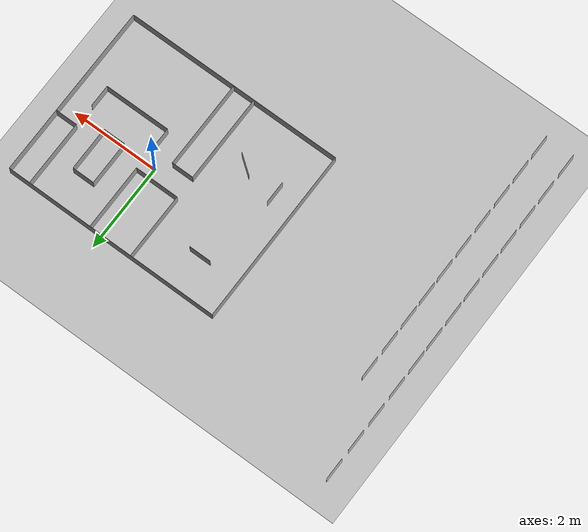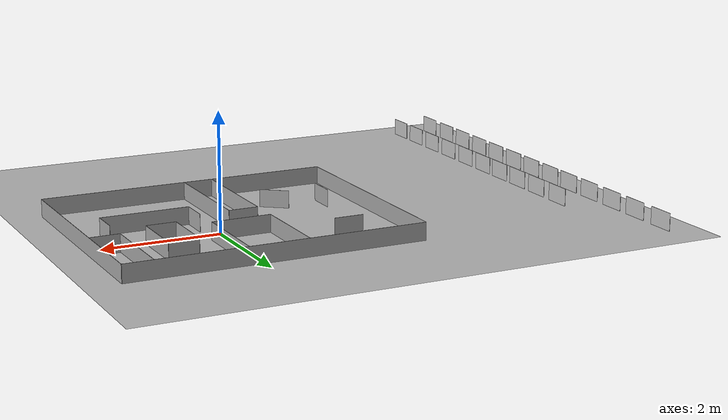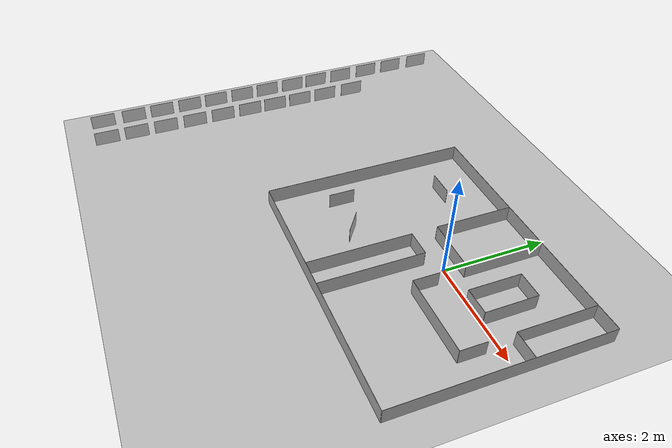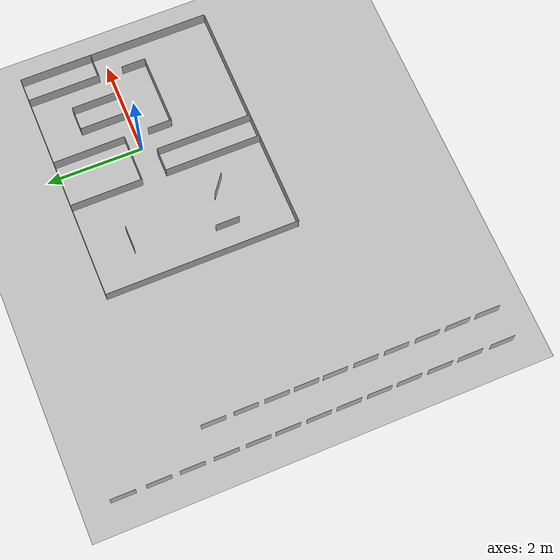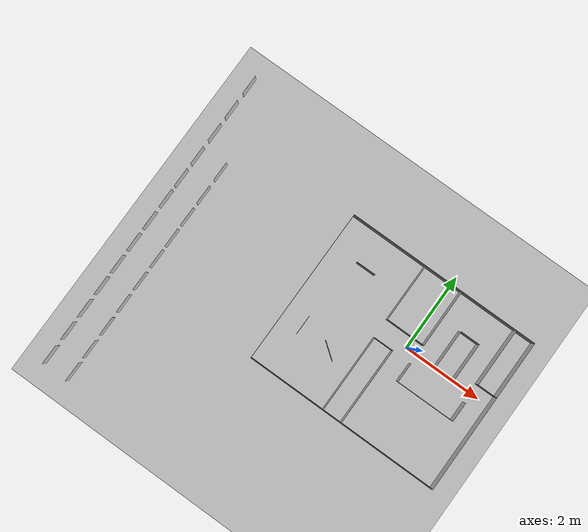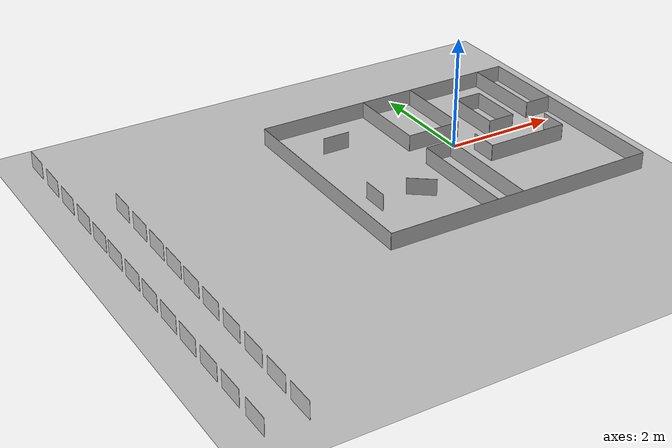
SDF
<sdf version="1.7">
 <world name="default">
  <light name="sun" type="directional">
   <pose>0 0 10 0 -0 0</pose>
   <diffuse>0.8 0.8 0.8 1</diffuse>
   <specular>0.2 0.2 0.2 1</specular>
   <attenuation>
    <range>1000</range>
    <constant>0.9</constant>
    <linear>0.01</linear>
    <quadratic>0.001</quadratic>
   </attenuation>
   <direction>-0.5 0.1 -0.9</direction>
   <spot><inner_angle>0</inner_angle><outer_angle>0</outer_angle><falloff>0</falloff></spot>
  </light>
  <model name="ground_plane">
   <static>1</static>
   <link name="link">
    <collision name="collision">
     <geometry><plane><normal>0 0 1</normal><size>100 100</size></plane></geometry>
     <surface>
      <contact><collide_bitmask>65535</collide_bitmask></contact>
      <friction><ode><mu>100</mu><mu2>50</mu2></ode></friction>
     </surface>
    </collision>
    <visual name="visual">
     <cast_shadows>0</cast_shadows>
     <geometry><plane><normal>0 0 1</normal><size>100 100</size></plane></geometry>
     <material>
      <script><uri>file://media/materials/scripts/gazebo.material</uri><name>Gazebo/Grey</name></script>
     </material>
    </visual>
   </link>
  </model>
  <gravity>0 0 -9.8</gravity>
  <magnetic_field>6e-06 2.3e-05 -4.2e-05</magnetic_field>
  <atmosphere type="adiabatic"/>
  <physics type="ode">
   <max_step_size>0.001</max_step_size>
   <real_time_factor>1</real_time_factor>
   <real_time_update_rate>1000</real_time_update_rate>
  </physics>
  <scene><ambient>0.4 0.4 0.4 1</ambient><background>0.7 0.7 0.7 1</background><shadows>1</shadows></scene>
  <spherical_coordinates>
   <surface_model>EARTH_WGS84</surface_model>
   <latitude_deg>0</latitude_deg>
   <longitude_deg>0</longitude_deg>
   <elevation>0</elevation>
   <heading_deg>0</heading_deg>
  </spherical_coordinates>
  <model name="boundary_5*0.3_clone">
   <link name="link">
    <inertial>
     <mass>1</mass>
     <inertia>
      <ixx>0.166667</ixx>
      <ixy>0</ixy>
      <ixz>0</ixz>
      <iyy>0.166667</iyy>
      <iyz>0</iyz>
      <izz>0.166667</izz>
     </inertia>
    </inertial>
    <visual name="visual">
     <geometry><box><size>5 0.005 0.3</size></box></geometry>
     <material>
      <script><name>Gazebo/Grey</name><uri>file://media/materials/scripts/gazebo.material</uri></script>
      <shader type="pixel"><normal_map>__default__</normal_map></shader>
      <ambient>0.3 0.3 0.3 1</ambient>
      <diffuse>0.7 0.7 0.7 1</diffuse>
      <specular>0.01 0.01 0.01 1</specular>
      <emissive>0 0 0 1</emissive>
     </material>
    </visual>
    <collision name="collision">
     <geometry><box><size>5 0.005 0.3</size></box></geometry>
     <surface>
      <friction>
       <ode><mu>1</mu><mu2>1</mu2><fdir1>0 0 0</fdir1><slip1>0</slip1><slip2>0</slip2></ode>
       <torsional>
        <coefficient>1</coefficient>
        <patch_radius>0</patch_radius>
        <surface_radius>0</surface_radius>
        <use_patch_radius>1</use_patch_radius>
        <ode><slip>0</slip></ode>
       </torsional>
      </friction>
      <bounce><restitution_coefficient>0</restitution_coefficient><threshold>1e+06</threshold></bounce>
      <contact>
       <collide_without_contact>0</collide_without_contact>
       <collide_without_contact_bitmask>1</collide_without_contact_bitmask>
       <collide_bitmask>1</collide_bitmask>
       <ode>
        <soft_cfm>0</soft_cfm>
        <soft_erp>0.2</soft_erp>
        <kp>1e+13</kp>
        <kd>1</kd>
        <max_vel>0.01</max_vel>
        <min_depth>0</min_depth>
       </ode>
       <bullet>
        <split_impulse>1</split_impulse>
        <split_impulse_penetration_threshold>-0.01</split_impulse_penetration_threshold>
        <soft_cfm>0</soft_cfm>
        <soft_erp>0.2</soft_erp>
        <kp>1e+13</kp>
        <kd>1</kd>
       </bullet>
      </contact>
     </surface>
    </collision>
   </link>
   <static>1</static>
   <pose>-0.256653 -2.25815 0.149981 -1e-06 7e-06 0.000393</pose>
  </model>
  <model name="boundry_4*0.3">
   <link name="link">
    <inertial>
     <mass>1</mass>
     <inertia>
      <ixx>0.166667</ixx>
      <ixy>0</ixy>
      <ixz>0</ixz>
      <iyy>0.166667</iyy>
      <iyz>0</iyz>
      <izz>0.166667</izz>
     </inertia>
    </inertial>
    <visual name="visual">
     <geometry><box><size>0.005 4 0.3</size></box></geometry>
     <material>
      <script><name>Gazebo/Grey</name><uri>file://media/materials/scripts/gazebo.material</uri></script>
      <shader type="pixel"><normal_map>__default__</normal_map></shader>
      <ambient>0.3 0.3 0.3 1</ambient>
      <diffuse>0.7 0.7 0.7 1</diffuse>
      <specular>0.01 0.01 0.01 1</specular>
      <emissive>0 0 0 1</emissive>
     </material>
    </visual>
    <collision name="collision">
     <geometry><box><size>0.005 4 0.3</size></box></geometry>
     <surface>
      <friction>
       <ode><mu>1</mu><mu2>1</mu2><fdir1>0 0 0</fdir1><slip1>0</slip1><slip2>0</slip2></ode>
       <torsional>
        <coefficient>1</coefficient>
        <patch_radius>0</patch_radius>
        <surface_radius>0</surface_radius>
        <use_patch_radius>1</use_patch_radius>
        <ode><slip>0</slip></ode>
       </torsional>
      </friction>
      <bounce><restitution_coefficient>0</restitution_coefficient><threshold>1e+06</threshold></bounce>
      <contact>
       <collide_without_contact>0</collide_without_contact>
       <collide_without_contact_bitmask>1</collide_without_contact_bitmask>
       <collide_bitmask>1</collide_bitmask>
       <ode>
        <soft_cfm>0</soft_cfm>
        <soft_erp>0.2</soft_erp>
        <kp>1e+13</kp>
        <kd>1</kd>
        <max_vel>0.01</max_vel>
        <min_depth>0</min_depth>
       </ode>
       <bullet>
        <split_impulse>1</split_impulse>
        <split_impulse_penetration_threshold>-0.01</split_impulse_penetration_threshold>
        <soft_cfm>0</soft_cfm>
        <soft_erp>0.2</soft_erp>
        <kp>1e+13</kp>
        <kd>1</kd>
       </bullet>
      </contact>
     </surface>
    </collision>
   </link>
   <static>1</static>
   <pose>-2.75267 -0.251158 0.15 0 0.000101 -5.8e-05</pose>
  </model>
  <model name="boundary_5*0.3">
   <link name="link">
    <inertial>
     <mass>1</mass>
     <inertia>
      <ixx>0.166667</ixx>
      <ixy>0</ixy>
      <ixz>0</ixz>
      <iyy>0.166667</iyy>
      <iyz>0</iyz>
      <izz>0.166667</izz>
     </inertia>
    </inertial>
    <visual name="visual">
     <geometry><box><size>5 0.005 0.3</size></box></geometry>
     <material>
      <script><name>Gazebo/Grey</name><uri>file://media/materials/scripts/gazebo.material</uri></script>
      <shader type="pixel"><normal_map>__default__</normal_map></shader>
      <ambient>0.3 0.3 0.3 1</ambient>
      <diffuse>0.7 0.7 0.7 1</diffuse>
      <specular>0.01 0.01 0.01 1</specular>
      <emissive>0 0 0 1</emissive>
     </material>
    </visual>
    <collision name="collision">
     <geometry><box><size>5 0.005 0.3</size></box></geometry>
     <surface>
      <friction>
       <ode><mu>1</mu><mu2>1</mu2><fdir1>0 0 0</fdir1><slip1>0</slip1><slip2>0</slip2></ode>
       <torsional>
        <coefficient>1</coefficient>
        <patch_radius>0</patch_radius>
        <surface_radius>0</surface_radius>
        <use_patch_radius>1</use_patch_radius>
        <ode><slip>0</slip></ode>
       </torsional>
      </friction>
      <bounce><restitution_coefficient>0</restitution_coefficient><threshold>1e+06</threshold></bounce>
      <contact>
       <collide_without_contact>0</collide_without_contact>
       <collide_without_contact_bitmask>1</collide_without_contact_bitmask>
       <collide_bitmask>1</collide_bitmask>
       <ode>
        <soft_cfm>0</soft_cfm>
        <soft_erp>0.2</soft_erp>
        <kp>1e+13</kp>
        <kd>1</kd>
        <max_vel>0.01</max_vel>
        <min_depth>0</min_depth>
       </ode>
       <bullet>
        <split_impulse>1</split_impulse>
        <split_impulse_penetration_threshold>-0.01</split_impulse_penetration_threshold>
        <soft_cfm>0</soft_cfm>
        <soft_erp>0.2</soft_erp>
        <kp>1e+13</kp>
        <kd>1</kd>
       </bullet>
      </contact>
     </surface>
    </collision>
   </link>
   <static>1</static>
   <pose>-0.25 1.75297 0.149981 2e-06 -6e-06 0.000154</pose>
  </model>
  <model name="boundry_4*0.3_clone">
   <link name="link">
    <inertial>
     <mass>1</mass>
     <inertia>
      <ixx>0.166667</ixx>
      <ixy>0</ixy>
      <ixz>0</ixz>
      <iyy>0.166667</iyy>
      <iyz>0</iyz>
      <izz>0.166667</izz>
     </inertia>
    </inertial>
    <visual name="visual">
     <geometry><box><size>0.005 4 0.3</size></box></geometry>
     <material>
      <script><name>Gazebo/Grey</name><uri>file://media/materials/scripts/gazebo.material</uri></script>
      <shader type="pixel"><normal_map>__default__</normal_map></shader>
      <ambient>0.3 0.3 0.3 1</ambient>
      <diffuse>0.7 0.7 0.7 1</diffuse>
      <specular>0.01 0.01 0.01 1</specular>
      <emissive>0 0 0 1</emissive>
     </material>
    </visual>
    <collision name="collision">
     <geometry><box><size>0.005 4 0.3</size></box></geometry>
     <surface>
      <friction>
       <ode><mu>1</mu><mu2>1</mu2><fdir1>0 0 0</fdir1><slip1>0</slip1><slip2>0</slip2></ode>
       <torsional>
        <coefficient>1</coefficient>
        <patch_radius>0</patch_radius>
        <surface_radius>0</surface_radius>
        <use_patch_radius>1</use_patch_radius>
        <ode><slip>0</slip></ode>
       </torsional>
      </friction>
      <bounce><restitution_coefficient>0</restitution_coefficient><threshold>1e+06</threshold></bounce>
      <contact>
       <collide_without_contact>0</collide_without_contact>
       <collide_without_contact_bitmask>1</collide_without_contact_bitmask>
       <collide_bitmask>1</collide_bitmask>
       <ode>
        <soft_cfm>0</soft_cfm>
        <soft_erp>0.2</soft_erp>
        <kp>1e+13</kp>
        <kd>1</kd>
        <max_vel>0.01</max_vel>
        <min_depth>0</min_depth>
       </ode>
       <bullet>
        <split_impulse>1</split_impulse>
        <split_impulse_penetration_threshold>-0.01</split_impulse_penetration_threshold>
        <soft_cfm>0</soft_cfm>
        <soft_erp>0.2</soft_erp>
        <kp>1e+13</kp>
        <kd>1</kd>
       </bullet>
      </contact>
     </surface>
    </collision>
   </link>
   <static>1</static>
   <pose>2.25266 -0.249739 0.15 -0 -0.000102 1e-05</pose>
  </model>
  <model name="boundry_1.5*0.3">
   <link name="link">
    <inertial>
     <mass>1</mass>
     <inertia>
      <ixx>0.166667</ixx>
      <ixy>0</ixy>
      <ixz>0</ixz>
      <iyy>0.166667</iyy>
      <iyz>0</iyz>
      <izz>0.166667</izz>
     </inertia>
    </inertial>
    <visual name="visual">
     <geometry><box><size>0.005 1.5 0.3</size></box></geometry>
     <material>
      <script><name>Gazebo/Grey</name><uri>file://media/materials/scripts/gazebo.material</uri></script>
      <shader type="pixel"><normal_map>__default__</normal_map></shader>
      <ambient>0.3 0.3 0.3 1</ambient>
      <diffuse>0.7 0.7 0.7 1</diffuse>
      <specular>0.01 0.01 0.01 1</specular>
      <emissive>0 0 0 1</emissive>
     </material>
    </visual>
    <collision name="collision">
     <geometry><box><size>0.005 1.5 0.3</size></box></geometry>
     <surface>
      <friction>
       <ode><mu>1</mu><mu2>1</mu2><fdir1>0 0 0</fdir1><slip1>0</slip1><slip2>0</slip2></ode>
       <torsional>
        <coefficient>1</coefficient>
        <patch_radius>0</patch_radius>
        <surface_radius>0</surface_radius>
        <use_patch_radius>1</use_patch_radius>
        <ode><slip>0</slip></ode>
       </torsional>
      </friction>
      <bounce><restitution_coefficient>0</restitution_coefficient><threshold>1e+06</threshold></bounce>
      <contact>
       <collide_without_contact>0</collide_without_contact>
       <collide_without_contact_bitmask>1</collide_without_contact_bitmask>
       <collide_bitmask>1</collide_bitmask>
       <ode>
        <soft_cfm>0</soft_cfm>
        <soft_erp>0.2</soft_erp>
        <kp>1e+13</kp>
        <kd>1</kd>
        <max_vel>0.01</max_vel>
        <min_depth>0</min_depth>
       </ode>
       <bullet>
        <split_impulse>1</split_impulse>
        <split_impulse_penetration_threshold>-0.01</split_impulse_penetration_threshold>
        <soft_cfm>0</soft_cfm>
        <soft_erp>0.2</soft_erp>
        <kp>1e+13</kp>
        <kd>1</kd>
       </bullet>
      </contact>
     </surface>
    </collision>
   </link>
   <static>1</static>
   <pose>-0.751257 1 0.149993 1e-05 5e-06 -0.001735</pose>
  </model>
  <model name="boundry_1.5*0.3_clone">
   <link name="link">
    <inertial>
     <mass>1</mass>
     <inertia>
      <ixx>0.166667</ixx>
      <ixy>0</ixy>
      <ixz>0</ixz>
      <iyy>0.166667</iyy>
      <iyz>0</iyz>
      <izz>0.166667</izz>
     </inertia>
    </inertial>
    <visual name="visual">
     <geometry><box><size>0.005 1.5 0.3</size></box></geometry>
     <material>
      <script><name>Gazebo/Grey</name><uri>file://media/materials/scripts/gazebo.material</uri></script>
      <shader type="pixel"><normal_map>__default__</normal_map></shader>
      <ambient>0.3 0.3 0.3 1</ambient>
      <diffuse>0.7 0.7 0.7 1</diffuse>
      <specular>0.01 0.01 0.01 1</specular>
      <emissive>0 0 0 1</emissive>
     </material>
    </visual>
    <collision name="collision">
     <geometry><box><size>0.005 1.5 0.3</size></box></geometry>
     <surface>
      <friction>
       <ode><mu>1</mu><mu2>1</mu2><fdir1>0 0 0</fdir1><slip1>0</slip1><slip2>0</slip2></ode>
       <torsional>
        <coefficient>1</coefficient>
        <patch_radius>0</patch_radius>
        <surface_radius>0</surface_radius>
        <use_patch_radius>1</use_patch_radius>
        <ode><slip>0</slip></ode>
       </torsional>
      </friction>
      <bounce><restitution_coefficient>0</restitution_coefficient><threshold>1e+06</threshold></bounce>
      <contact>
       <collide_without_contact>0</collide_without_contact>
       <collide_without_contact_bitmask>1</collide_without_contact_bitmask>
       <collide_bitmask>1</collide_bitmask>
       <ode>
        <soft_cfm>0</soft_cfm>
        <soft_erp>0.2</soft_erp>
        <kp>1e+13</kp>
        <kd>1</kd>
        <max_vel>0.01</max_vel>
        <min_depth>0</min_depth>
       </ode>
       <bullet>
        <split_impulse>1</split_impulse>
        <split_impulse_penetration_threshold>-0.01</split_impulse_penetration_threshold>
        <soft_cfm>0</soft_cfm>
        <soft_erp>0.2</soft_erp>
        <kp>1e+13</kp>
        <kd>1</kd>
       </bullet>
      </contact>
     </surface>
    </collision>
   </link>
   <static>1</static>
   <pose>0.250874 0.999816 0.15 0 -1.5e-05 0.002246</pose>
  </model>
  <model name="boundry_1.5*0.3_clone_0">
   <link name="link">
    <inertial>
     <mass>1</mass>
     <inertia>
      <ixx>0.166667</ixx>
      <ixy>0</ixy>
      <ixz>0</ixz>
      <iyy>0.166667</iyy>
      <iyz>0</iyz>
      <izz>0.166667</izz>
     </inertia>
    </inertial>
    <visual name="visual">
     <geometry><box><size>0.005 1.5 0.3</size></box></geometry>
     <material>
      <script><name>Gazebo/Grey</name><uri>file://media/materials/scripts/gazebo.material</uri></script>
      <shader type="pixel"><normal_map>__default__</normal_map></shader>
      <ambient>0.3 0.3 0.3 1</ambient>
      <diffuse>0.7 0.7 0.7 1</diffuse>
      <specular>0.01 0.01 0.01 1</specular>
      <emissive>0 0 0 1</emissive>
     </material>
    </visual>
    <collision name="collision">
     <geometry><box><size>0.005 1.5 0.3</size></box></geometry>
     <surface>
      <friction>
       <ode><mu>1</mu><mu2>1</mu2><fdir1>0 0 0</fdir1><slip1>0</slip1><slip2>0</slip2></ode>
       <torsional>
        <coefficient>1</coefficient>
        <patch_radius>0</patch_radius>
        <surface_radius>0</surface_radius>
        <use_patch_radius>1</use_patch_radius>
        <ode><slip>0</slip></ode>
       </torsional>
      </friction>
      <bounce><restitution_coefficient>0</restitution_coefficient><threshold>1e+06</threshold></bounce>
      <contact>
       <collide_without_contact>0</collide_without_contact>
       <collide_without_contact_bitmask>1</collide_without_contact_bitmask>
       <collide_bitmask>1</collide_bitmask>
       <ode>
        <soft_cfm>0</soft_cfm>
        <soft_erp>0.2</soft_erp>
        <kp>1e+13</kp>
        <kd>1</kd>
        <max_vel>0.01</max_vel>
        <min_depth>0</min_depth>
       </ode>
       <bullet>
        <split_impulse>1</split_impulse>
        <split_impulse_penetration_threshold>-0.01</split_impulse_penetration_threshold>
        <soft_cfm>0</soft_cfm>
        <soft_erp>0.2</soft_erp>
        <kp>1e+13</kp>
        <kd>1</kd>
       </bullet>
      </contact>
     </surface>
    </collision>
   </link>
   <static>1</static>
   <pose>1.75004 1.00038 0.15 0 8e-06 -5.8e-05</pose>
  </model>
  <model name="boundry_2*0.3">
   <link name="link">
    <inertial>
     <mass>1</mass>
     <inertia>
      <ixx>0.166667</ixx>
      <ixy>0</ixy>
      <ixz>0</ixz>
      <iyy>0.166667</iyy>
      <iyz>0</iyz>
      <izz>0.166667</izz>
     </inertia>
    </inertial>
    <visual name="visual">
     <geometry><box><size>0.005 2 0.3</size></box></geometry>
     <material>
      <script><name>Gazebo/Grey</name><uri>file://media/materials/scripts/gazebo.material</uri></script>
      <shader type="pixel"><normal_map>__default__</normal_map></shader>
      <ambient>0.3 0.3 0.3 1</ambient>
      <diffuse>0.7 0.7 0.7 1</diffuse>
      <specular>0.01 0.01 0.01 1</specular>
      <emissive>0 0 0 1</emissive>
     </material>
    </visual>
    <collision name="collision">
     <geometry><box><size>0.005 2 0.3</size></box></geometry>
     <surface>
      <friction>
       <ode><mu>1</mu><mu2>1</mu2><fdir1>0 0 0</fdir1><slip1>0</slip1><slip2>0</slip2></ode>
       <torsional>
        <coefficient>1</coefficient>
        <patch_radius>0</patch_radius>
        <surface_radius>0</surface_radius>
        <use_patch_radius>1</use_patch_radius>
        <ode><slip>0</slip></ode>
       </torsional>
      </friction>
      <bounce><restitution_coefficient>0</restitution_coefficient><threshold>1e+06</threshold></bounce>
      <contact>
       <collide_without_contact>0</collide_without_contact>
       <collide_without_contact_bitmask>1</collide_without_contact_bitmask>
       <collide_bitmask>1</collide_bitmask>
       <ode>
        <soft_cfm>0</soft_cfm>
        <soft_erp>0.2</soft_erp>
        <kp>1e+13</kp>
        <kd>1</kd>
        <max_vel>0.01</max_vel>
        <min_depth>0</min_depth>
       </ode>
       <bullet>
        <split_impulse>1</split_impulse>
        <split_impulse_penetration_threshold>-0.01</split_impulse_penetration_threshold>
        <soft_cfm>0</soft_cfm>
        <soft_erp>0.2</soft_erp>
        <kp>1e+13</kp>
        <kd>1</kd>
       </bullet>
      </contact>
     </surface>
    </collision>
   </link>
   <static>1</static>
   <pose>-0.750005 -1.25517 0.149981 -1.9e-05 -1e-06 -6e-06</pose>
  </model>
  <model name="boundry_2*0.3_clone">
   <link name="link">
    <inertial>
     <mass>1</mass>
     <inertia>
      <ixx>0.166667</ixx>
      <ixy>0</ixy>
      <ixz>0</ixz>
      <iyy>0.166667</iyy>
      <iyz>0</iyz>
      <izz>0.166667</izz>
     </inertia>
    </inertial>
    <visual name="visual">
     <geometry><box><size>0.005 2 0.3</size></box></geometry>
     <material>
      <script><name>Gazebo/Grey</name><uri>file://media/materials/scripts/gazebo.material</uri></script>
      <shader type="pixel"><normal_map>__default__</normal_map></shader>
      <ambient>0.3 0.3 0.3 1</ambient>
      <diffuse>0.7 0.7 0.7 1</diffuse>
      <specular>0.01 0.01 0.01 1</specular>
      <emissive>0 0 0 1</emissive>
     </material>
    </visual>
    <collision name="collision">
     <geometry><box><size>0.005 2 0.3</size></box></geometry>
     <surface>
      <friction>
       <ode><mu>1</mu><mu2>1</mu2><fdir1>0 0 0</fdir1><slip1>0</slip1><slip2>0</slip2></ode>
       <torsional>
        <coefficient>1</coefficient>
        <patch_radius>0</patch_radius>
        <surface_radius>0</surface_radius>
        <use_patch_radius>1</use_patch_radius>
        <ode><slip>0</slip></ode>
       </torsional>
      </friction>
      <bounce><restitution_coefficient>0</restitution_coefficient><threshold>1e+06</threshold></bounce>
      <contact>
       <collide_without_contact>0</collide_without_contact>
       <collide_without_contact_bitmask>1</collide_without_contact_bitmask>
       <collide_bitmask>1</collide_bitmask>
       <ode>
        <soft_cfm>0</soft_cfm>
        <soft_erp>0.2</soft_erp>
        <kp>1e+13</kp>
        <kd>1</kd>
        <max_vel>0.01</max_vel>
        <min_depth>0</min_depth>
       </ode>
       <bullet>
        <split_impulse>1</split_impulse>
        <split_impulse_penetration_threshold>-0.01</split_impulse_penetration_threshold>
        <soft_cfm>0</soft_cfm>
        <soft_erp>0.2</soft_erp>
        <kp>1e+13</kp>
        <kd>1</kd>
       </bullet>
      </contact>
     </surface>
    </collision>
   </link>
   <static>1</static>
   <pose>-0.249943 -1.2555 0.149945 -5.5e-05 -0.000133 -0.000347</pose>
  </model>
  <model name="boundry_1.5*0.3_clone_clone">
   <link name="link">
    <inertial>
     <mass>1</mass>
     <inertia>
      <ixx>0.166667</ixx>
      <ixy>0</ixy>
      <ixz>0</ixz>
      <iyy>0.166667</iyy>
      <iyz>0</iyz>
      <izz>0.166667</izz>
     </inertia>
    </inertial>
    <visual name="visual">
     <geometry><box><size>0.005 1.5 0.3</size></box></geometry>
     <material>
      <script><name>Gazebo/Grey</name><uri>file://media/materials/scripts/gazebo.material</uri></script>
      <shader type="pixel"><normal_map>__default__</normal_map></shader>
      <ambient>0.3 0.3 0.3 1</ambient>
      <diffuse>0.7 0.7 0.7 1</diffuse>
      <specular>0.01 0.01 0.01 1</specular>
      <emissive>0 0 0 1</emissive>
     </material>
    </visual>
    <collision name="collision">
     <geometry><box><size>0.005 1.5 0.3</size></box></geometry>
     <surface>
      <friction>
       <ode><mu>1</mu><mu2>1</mu2><fdir1>0 0 0</fdir1><slip1>0</slip1><slip2>0</slip2></ode>
       <torsional>
        <coefficient>1</coefficient>
        <patch_radius>0</patch_radius>
        <surface_radius>0</surface_radius>
        <use_patch_radius>1</use_patch_radius>
        <ode><slip>0</slip></ode>
       </torsional>
      </friction>
      <bounce><restitution_coefficient>0</restitution_coefficient><threshold>1e+06</threshold></bounce>
      <contact>
       <collide_without_contact>0</collide_without_contact>
       <collide_without_contact_bitmask>1</collide_without_contact_bitmask>
       <collide_bitmask>1</collide_bitmask>
       <ode>
        <soft_cfm>0</soft_cfm>
        <soft_erp>0.2</soft_erp>
        <kp>1e+13</kp>
        <kd>1</kd>
        <max_vel>0.01</max_vel>
        <min_depth>0</min_depth>
       </ode>
       <bullet>
        <split_impulse>1</split_impulse>
        <split_impulse_penetration_threshold>-0.01</split_impulse_penetration_threshold>
        <soft_cfm>0</soft_cfm>
        <soft_erp>0.2</soft_erp>
        <kp>1e+13</kp>
        <kd>1</kd>
       </bullet>
      </contact>
     </surface>
    </collision>
   </link>
   <static>1</static>
   <pose>0.999383 -0.750677 0.149989 1.9e-05 -0.001043 1.57282</pose>
  </model>
  <model name="boundary_1*0.3">
   <link name="link">
    <inertial>
     <mass>1</mass>
     <inertia>
      <ixx>0.166667</ixx>
      <ixy>0</ixy>
      <ixz>0</ixz>
      <iyy>0.166667</iyy>
      <iyz>0</iyz>
      <izz>0.166667</izz>
     </inertia>
    </inertial>
    <visual name="visual">
     <geometry><box><size>1 0.005 0.3</size></box></geometry>
     <material>
      <script><name>Gazebo/Grey</name><uri>file://media/materials/scripts/gazebo.material</uri></script>
      <shader type="pixel"><normal_map>__default__</normal_map></shader>
      <ambient>0.3 0.3 0.3 1</ambient>
      <diffuse>0.7 0.7 0.7 1</diffuse>
      <specular>0.01 0.01 0.01 1</specular>
      <emissive>0 0 0 1</emissive>
     </material>
    </visual>
    <collision name="collision">
     <geometry><box><size>1 0.005 0.3</size></box></geometry>
     <surface>
      <friction>
       <ode><mu>1</mu><mu2>1</mu2><fdir1>0 0 0</fdir1><slip1>0</slip1><slip2>0</slip2></ode>
       <torsional>
        <coefficient>1</coefficient>
        <patch_radius>0</patch_radius>
        <surface_radius>0</surface_radius>
        <use_patch_radius>1</use_patch_radius>
        <ode><slip>0</slip></ode>
       </torsional>
      </friction>
      <bounce><restitution_coefficient>0</restitution_coefficient><threshold>1e+06</threshold></bounce>
      <contact>
       <collide_without_contact>0</collide_without_contact>
       <collide_without_contact_bitmask>1</collide_without_contact_bitmask>
       <collide_bitmask>1</collide_bitmask>
       <ode>
        <soft_cfm>0</soft_cfm>
        <soft_erp>0.2</soft_erp>
        <kp>1e+13</kp>
        <kd>1</kd>
        <max_vel>0.01</max_vel>
        <min_depth>0</min_depth>
       </ode>
       <bullet>
        <split_impulse>1</split_impulse>
        <split_impulse_penetration_threshold>-0.01</split_impulse_penetration_threshold>
        <soft_cfm>0</soft_cfm>
        <soft_erp>0.2</soft_erp>
        <kp>1e+13</kp>
        <kd>1</kd>
       </bullet>
      </contact>
     </surface>
    </collision>
   </link>
   <static>1</static>
   <pose>-0.249996 0.252503 0.15 -7e-06 -0 -0.001728</pose>
  </model>
  <model name="boundary_0.5*0.3">
   <link name="link">
    <inertial>
     <mass>1</mass>
     <inertia>
      <ixx>0.166667</ixx>
      <ixy>0</ixy>
      <ixz>0</ixz>
      <iyy>0.166667</iyy>
      <iyz>0</iyz>
      <izz>0.166667</izz>
     </inertia>
    </inertial>
    <visual name="visual">
     <geometry><box><size>0.5 0.005 0.3</size></box></geometry>
     <material>
      <script><name>Gazebo/Grey</name><uri>file://media/materials/scripts/gazebo.material</uri></script>
      <shader type="pixel"><normal_map>__default__</normal_map></shader>
      <ambient>0.3 0.3 0.3 1</ambient>
      <diffuse>0.7 0.7 0.7 1</diffuse>
      <specular>0.01 0.01 0.01 1</specular>
      <emissive>0 0 0 1</emissive>
     </material>
    </visual>
    <collision name="collision">
     <geometry><box><size>0.5 0.005 0.3</size></box></geometry>
     <surface>
      <friction>
       <ode><mu>1</mu><mu2>1</mu2><fdir1>0 0 0</fdir1><slip1>0</slip1><slip2>0</slip2></ode>
       <torsional>
        <coefficient>1</coefficient>
        <patch_radius>0</patch_radius>
        <surface_radius>0</surface_radius>
        <use_patch_radius>1</use_patch_radius>
        <ode><slip>0</slip></ode>
       </torsional>
      </friction>
      <bounce><restitution_coefficient>0</restitution_coefficient><threshold>1e+06</threshold></bounce>
      <contact>
       <collide_without_contact>0</collide_without_contact>
       <collide_without_contact_bitmask>1</collide_without_contact_bitmask>
       <collide_bitmask>1</collide_bitmask>
       <ode>
        <soft_cfm>0</soft_cfm>
        <soft_erp>0.2</soft_erp>
        <kp>1e+13</kp>
        <kd>1</kd>
        <max_vel>0.01</max_vel>
        <min_depth>0</min_depth>
       </ode>
       <bullet>
        <split_impulse>1</split_impulse>
        <split_impulse_penetration_threshold>-0.01</split_impulse_penetration_threshold>
        <soft_cfm>0</soft_cfm>
        <soft_erp>0.2</soft_erp>
        <kp>1e+13</kp>
        <kd>1</kd>
       </bullet>
      </contact>
     </surface>
    </collision>
   </link>
   <static>1</static>
   <pose>-0.500033 -0.252549 0.15 0 -0 0.000201</pose>
  </model>
  <model name="boundary_0.5*0.3_clone">
   <link name="link">
    <inertial>
     <mass>1</mass>
     <inertia>
      <ixx>0.166667</ixx>
      <ixy>0</ixy>
      <ixz>0</ixz>
      <iyy>0.166667</iyy>
      <iyz>0</iyz>
      <izz>0.166667</izz>
     </inertia>
    </inertial>
    <visual name="visual">
     <geometry><box><size>0.5 0.005 0.3</size></box></geometry>
     <material>
      <script><name>Gazebo/Grey</name><uri>file://media/materials/scripts/gazebo.material</uri></script>
      <shader type="pixel"><normal_map>__default__</normal_map></shader>
      <ambient>0.3 0.3 0.3 1</ambient>
      <diffuse>0.7 0.7 0.7 1</diffuse>
      <specular>0.01 0.01 0.01 1</specular>
      <emissive>0 0 0 1</emissive>
     </material>
    </visual>
    <collision name="collision">
     <geometry><box><size>0.5 0.005 0.3</size></box></geometry>
     <surface>
      <friction>
       <ode><mu>1</mu><mu2>1</mu2><fdir1>0 0 0</fdir1><slip1>0</slip1><slip2>0</slip2></ode>
       <torsional>
        <coefficient>1</coefficient>
        <patch_radius>0</patch_radius>
        <surface_radius>0</surface_radius>
        <use_patch_radius>1</use_patch_radius>
        <ode><slip>0</slip></ode>
       </torsional>
      </friction>
      <bounce><restitution_coefficient>0</restitution_coefficient><threshold>1e+06</threshold></bounce>
      <contact>
       <collide_without_contact>0</collide_without_contact>
       <collide_without_contact_bitmask>1</collide_without_contact_bitmask>
       <collide_bitmask>1</collide_bitmask>
       <ode>
        <soft_cfm>0</soft_cfm>
        <soft_erp>0.2</soft_erp>
        <kp>1e+13</kp>
        <kd>1</kd>
        <max_vel>0.01</max_vel>
        <min_depth>0</min_depth>
       </ode>
       <bullet>
        <split_impulse>1</split_impulse>
        <split_impulse_penetration_threshold>-0.01</split_impulse_penetration_threshold>
        <soft_cfm>0</soft_cfm>
        <soft_erp>0.2</soft_erp>
        <kp>1e+13</kp>
        <kd>1</kd>
       </bullet>
      </contact>
     </surface>
    </collision>
   </link>
   <static>1</static>
   <pose>2 0.248459 0.149998 -0 -8e-06 0.002353</pose>
  </model>
  <model name="boundary_0.5*0.3_clone_clone">
   <link name="link">
    <inertial>
     <mass>1</mass>
     <inertia>
      <ixx>0.166667</ixx>
      <ixy>0</ixy>
      <ixz>0</ixz>
      <iyy>0.166667</iyy>
      <iyz>0</iyz>
      <izz>0.166667</izz>
     </inertia>
    </inertial>
    <visual name="visual">
     <geometry><box><size>0.5 0.005 0.3</size></box></geometry>
     <material>
      <script><name>Gazebo/Grey</name><uri>file://media/materials/scripts/gazebo.material</uri></script>
      <shader type="pixel"><normal_map>__default__</normal_map></shader>
      <ambient>0.3 0.3 0.3 1</ambient>
      <diffuse>0.7 0.7 0.7 1</diffuse>
      <specular>0.01 0.01 0.01 1</specular>
      <emissive>0 0 0 1</emissive>
     </material>
    </visual>
    <collision name="collision">
     <geometry><box><size>0.5 0.005 0.3</size></box></geometry>
     <surface>
      <friction>
       <ode><mu>1</mu><mu2>1</mu2><fdir1>0 0 0</fdir1><slip1>0</slip1><slip2>0</slip2></ode>
       <torsional>
        <coefficient>1</coefficient>
        <patch_radius>0</patch_radius>
        <surface_radius>0</surface_radius>
        <use_patch_radius>1</use_patch_radius>
        <ode><slip>0</slip></ode>
       </torsional>
      </friction>
      <bounce><restitution_coefficient>0</restitution_coefficient><threshold>1e+06</threshold></bounce>
      <contact>
       <collide_without_contact>0</collide_without_contact>
       <collide_without_contact_bitmask>1</collide_without_contact_bitmask>
       <collide_bitmask>1</collide_bitmask>
       <ode>
        <soft_cfm>0</soft_cfm>
        <soft_erp>0.2</soft_erp>
        <kp>1e+13</kp>
        <kd>1</kd>
        <max_vel>0.01</max_vel>
        <min_depth>0</min_depth>
       </ode>
       <bullet>
        <split_impulse>1</split_impulse>
        <split_impulse_penetration_threshold>-0.01</split_impulse_penetration_threshold>
        <soft_cfm>0</soft_cfm>
        <soft_erp>0.2</soft_erp>
        <kp>1e+13</kp>
        <kd>1</kd>
       </bullet>
      </contact>
     </surface>
    </collision>
   </link>
   <static>1</static>
   <pose>0.999512 -0.001259 0.15 0 -0 0.001461</pose>
  </model>
  <model name="boundary_0.5*0.3_clone_clone_0">
   <link name="link">
    <inertial>
     <mass>1</mass>
     <inertia>
      <ixx>0.166667</ixx>
      <ixy>0</ixy>
      <ixz>0</ixz>
      <iyy>0.166667</iyy>
      <iyz>0</iyz>
      <izz>0.166667</izz>
     </inertia>
    </inertial>
    <visual name="visual">
     <geometry><box><size>0.5 0.005 0.3</size></box></geometry>
     <material>
      <script><name>Gazebo/Grey</name><uri>file://media/materials/scripts/gazebo.material</uri></script>
      <shader type="pixel"><normal_map>__default__</normal_map></shader>
      <ambient>0.3 0.3 0.3 1</ambient>
      <diffuse>0.7 0.7 0.7 1</diffuse>
      <specular>0.01 0.01 0.01 1</specular>
      <emissive>0 0 0 1</emissive>
     </material>
    </visual>
    <collision name="collision">
     <geometry><box><size>0.5 0.005 0.3</size></box></geometry>
     <surface>
      <friction>
       <ode><mu>1</mu><mu2>1</mu2><fdir1>0 0 0</fdir1><slip1>0</slip1><slip2>0</slip2></ode>
       <torsional>
        <coefficient>1</coefficient>
        <patch_radius>0</patch_radius>
        <surface_radius>0</surface_radius>
        <use_patch_radius>1</use_patch_radius>
        <ode><slip>0</slip></ode>
       </torsional>
      </friction>
      <bounce><restitution_coefficient>0</restitution_coefficient><threshold>1e+06</threshold></bounce>
      <contact>
       <collide_without_contact>0</collide_without_contact>
       <collide_without_contact_bitmask>1</collide_without_contact_bitmask>
       <collide_bitmask>1</collide_bitmask>
       <ode>
        <soft_cfm>0</soft_cfm>
        <soft_erp>0.2</soft_erp>
        <kp>1e+13</kp>
        <kd>1</kd>
        <max_vel>0.01</max_vel>
        <min_depth>0</min_depth>
       </ode>
       <bullet>
        <split_impulse>1</split_impulse>
        <split_impulse_penetration_threshold>-0.01</split_impulse_penetration_threshold>
        <soft_cfm>0</soft_cfm>
        <soft_erp>0.2</soft_erp>
        <kp>1e+13</kp>
        <kd>1</kd>
       </bullet>
      </contact>
     </surface>
    </collision>
   </link>
   <static>1</static>
   <pose>1.0005 1.00126 0.15 3e-06 -0 0.001415</pose>
  </model>
  <model name="boundary_1*0.3_clone">
   <link name="link">
    <inertial>
     <mass>1</mass>
     <inertia>
      <ixx>0.166667</ixx>
      <ixy>0</ixy>
      <ixz>0</ixz>
      <iyy>0.166667</iyy>
      <iyz>0</iyz>
      <izz>0.166667</izz>
     </inertia>
    </inertial>
    <visual name="visual">
     <geometry><box><size>1 0.005 0.3</size></box></geometry>
     <material>
      <script><name>Gazebo/Grey</name><uri>file://media/materials/scripts/gazebo.material</uri></script>
      <shader type="pixel"><normal_map>__default__</normal_map></shader>
      <ambient>0.3 0.3 0.3 1</ambient>
      <diffuse>0.7 0.7 0.7 1</diffuse>
      <specular>0.01 0.01 0.01 1</specular>
      <emissive>0 0 0 1</emissive>
     </material>
    </visual>
    <collision name="collision">
     <geometry><box><size>1 0.005 0.3</size></box></geometry>
     <surface>
      <friction>
       <ode><mu>1</mu><mu2>1</mu2><fdir1>0 0 0</fdir1><slip1>0</slip1><slip2>0</slip2></ode>
       <torsional>
        <coefficient>1</coefficient>
        <patch_radius>0</patch_radius>
        <surface_radius>0</surface_radius>
        <use_patch_radius>1</use_patch_radius>
        <ode><slip>0</slip></ode>
       </torsional>
      </friction>
      <bounce><restitution_coefficient>0</restitution_coefficient><threshold>1e+06</threshold></bounce>
      <contact>
       <collide_without_contact>0</collide_without_contact>
       <collide_without_contact_bitmask>1</collide_without_contact_bitmask>
       <collide_bitmask>1</collide_bitmask>
       <ode>
        <soft_cfm>0</soft_cfm>
        <soft_erp>0.2</soft_erp>
        <kp>1e+13</kp>
        <kd>1</kd>
        <max_vel>0.01</max_vel>
        <min_depth>0</min_depth>
       </ode>
       <bullet>
        <split_impulse>1</split_impulse>
        <split_impulse_penetration_threshold>-0.01</split_impulse_penetration_threshold>
        <soft_cfm>0</soft_cfm>
        <soft_erp>0.2</soft_erp>
        <kp>1e+13</kp>
        <kd>1</kd>
       </bullet>
      </contact>
     </surface>
    </collision>
   </link>
   <static>1</static>
   <pose>1.25126 0.499092 0.15 -2e-06 -0 1.57231</pose>
  </model>
  <model name="boundary_1*0.3_clone_clone">
   <link name="link">
    <inertial>
     <mass>1</mass>
     <inertia>
      <ixx>0.166667</ixx>
      <ixy>0</ixy>
      <ixz>0</ixz>
      <iyy>0.166667</iyy>
      <iyz>0</iyz>
      <izz>0.166667</izz>
     </inertia>
    </inertial>
    <visual name="visual">
     <geometry><box><size>1 0.005 0.3</size></box></geometry>
     <material>
      <script><name>Gazebo/Grey</name><uri>file://media/materials/scripts/gazebo.material</uri></script>
      <shader type="pixel"><normal_map>__default__</normal_map></shader>
      <ambient>0.3 0.3 0.3 1</ambient>
      <diffuse>0.7 0.7 0.7 1</diffuse>
      <specular>0.01 0.01 0.01 1</specular>
      <emissive>0 0 0 1</emissive>
     </material>
    </visual>
    <collision name="collision">
     <geometry><box><size>1 0.005 0.3</size></box></geometry>
     <surface>
      <friction>
       <ode><mu>1</mu><mu2>1</mu2><fdir1>0 0 0</fdir1><slip1>0</slip1><slip2>0</slip2></ode>
       <torsional>
        <coefficient>1</coefficient>
        <patch_radius>0</patch_radius>
        <surface_radius>0</surface_radius>
        <use_patch_radius>1</use_patch_radius>
        <ode><slip>0</slip></ode>
       </torsional>
      </friction>
      <bounce><restitution_coefficient>0</restitution_coefficient><threshold>1e+06</threshold></bounce>
      <contact>
       <collide_without_contact>0</collide_without_contact>
       <collide_without_contact_bitmask>1</collide_without_contact_bitmask>
       <collide_bitmask>1</collide_bitmask>
       <ode>
        <soft_cfm>0</soft_cfm>
        <soft_erp>0.2</soft_erp>
        <kp>1e+13</kp>
        <kd>1</kd>
        <max_vel>0.01</max_vel>
        <min_depth>0</min_depth>
       </ode>
       <bullet>
        <split_impulse>1</split_impulse>
        <split_impulse_penetration_threshold>-0.01</split_impulse_penetration_threshold>
        <soft_cfm>0</soft_cfm>
        <soft_erp>0.2</soft_erp>
        <kp>1e+13</kp>
        <kd>1</kd>
       </bullet>
      </contact>
     </surface>
    </collision>
   </link>
   <static>1</static>
   <pose>0.748752 0.500909 0.15 9e-06 -0 1.57232</pose>
  </model>
  <model name="boundary_0.5*0.3_clone_clone_clone">
   <link name="link">
    <inertial>
     <mass>1</mass>
     <inertia>
      <ixx>0.166667</ixx>
      <ixy>0</ixy>
      <ixz>0</ixz>
      <iyy>0.166667</iyy>
      <iyz>0</iyz>
      <izz>0.166667</izz>
     </inertia>
    </inertial>
    <visual name="visual">
     <geometry><box><size>0.5 0.005 0.3</size></box></geometry>
     <material>
      <script><name>Gazebo/Grey</name><uri>file://media/materials/scripts/gazebo.material</uri></script>
      <shader type="pixel"><normal_map>__default__</normal_map></shader>
      <ambient>0.3 0.3 0.3 1</ambient>
      <diffuse>0.7 0.7 0.7 1</diffuse>
      <specular>0.01 0.01 0.01 1</specular>
      <emissive>0 0 0 1</emissive>
     </material>
    </visual>
    <collision name="collision">
     <geometry><box><size>0.5 0.005 0.3</size></box></geometry>
     <surface>
      <friction>
       <ode><mu>1</mu><mu2>1</mu2><fdir1>0 0 0</fdir1><slip1>0</slip1><slip2>0</slip2></ode>
       <torsional>
        <coefficient>1</coefficient>
        <patch_radius>0</patch_radius>
        <surface_radius>0</surface_radius>
        <use_patch_radius>1</use_patch_radius>
        <ode><slip>0</slip></ode>
       </torsional>
      </friction>
      <bounce><restitution_coefficient>0</restitution_coefficient><threshold>1e+06</threshold></bounce>
      <contact>
       <collide_without_contact>0</collide_without_contact>
       <collide_without_contact_bitmask>1</collide_without_contact_bitmask>
       <collide_bitmask>1</collide_bitmask>
       <ode>
        <soft_cfm>0</soft_cfm>
        <soft_erp>0.2</soft_erp>
        <kp>1e+13</kp>
        <kd>1</kd>
        <max_vel>0.01</max_vel>
        <min_depth>0</min_depth>
       </ode>
       <bullet>
        <split_impulse>1</split_impulse>
        <split_impulse_penetration_threshold>-0.01</split_impulse_penetration_threshold>
        <soft_cfm>0</soft_cfm>
        <soft_erp>0.2</soft_erp>
        <kp>1e+13</kp>
        <kd>1</kd>
       </bullet>
      </contact>
     </surface>
    </collision>
   </link>
   <static>1</static>
   <pose>1.75308 -0.499624 0.150004 0.001398 -2e-06 1.57019</pose>
  </model>
  <model name="boundary_0.5*0.3_clone_clone_clone_clone">
   <link name="link">
    <inertial>
     <mass>1</mass>
     <inertia>
      <ixx>0.166667</ixx>
      <ixy>0</ixy>
      <ixz>0</ixz>
      <iyy>0.166667</iyy>
      <iyz>0</iyz>
      <izz>0.166667</izz>
     </inertia>
    </inertial>
    <visual name="visual">
     <geometry><box><size>0.5 0.005 0.3</size></box></geometry>
     <material>
      <script><name>Gazebo/Grey</name><uri>file://media/materials/scripts/gazebo.material</uri></script>
      <shader type="pixel"><normal_map>__default__</normal_map></shader>
      <ambient>0.3 0.3 0.3 1</ambient>
      <diffuse>0.7 0.7 0.7 1</diffuse>
      <specular>0.01 0.01 0.01 1</specular>
      <emissive>0 0 0 1</emissive>
     </material>
    </visual>
    <collision name="collision">
     <geometry><box><size>0.5 0.005 0.3</size></box></geometry>
     <surface>
      <friction>
       <ode><mu>1</mu><mu2>1</mu2><fdir1>0 0 0</fdir1><slip1>0</slip1><slip2>0</slip2></ode>
       <torsional>
        <coefficient>1</coefficient>
        <patch_radius>0</patch_radius>
        <surface_radius>0</surface_radius>
        <use_patch_radius>1</use_patch_radius>
        <ode><slip>0</slip></ode>
       </torsional>
      </friction>
      <bounce><restitution_coefficient>0</restitution_coefficient><threshold>1e+06</threshold></bounce>
      <contact>
       <collide_without_contact>0</collide_without_contact>
       <collide_without_contact_bitmask>1</collide_without_contact_bitmask>
       <collide_bitmask>1</collide_bitmask>
       <ode>
        <soft_cfm>0</soft_cfm>
        <soft_erp>0.2</soft_erp>
        <kp>1e+13</kp>
        <kd>1</kd>
        <max_vel>0.01</max_vel>
        <min_depth>0</min_depth>
       </ode>
       <bullet>
        <split_impulse>1</split_impulse>
        <split_impulse_penetration_threshold>-0.01</split_impulse_penetration_threshold>
        <soft_cfm>0</soft_cfm>
        <soft_erp>0.2</soft_erp>
        <kp>1e+13</kp>
        <kd>1</kd>
       </bullet>
      </contact>
     </surface>
    </collision>
   </link>
   <static>1</static>
   <pose>0.249625 -0.499054 0.15 8.1e-05 0 1.56747</pose>
  </model>
  <model name="boundary_0.5*0.3_clone_clone_clone_clone_0">
   <link name="link">
    <inertial>
     <mass>1</mass>
     <inertia>
      <ixx>0.166667</ixx>
      <ixy>0</ixy>
      <ixz>0</ixz>
      <iyy>0.166667</iyy>
      <iyz>0</iyz>
      <izz>0.166667</izz>
     </inertia>
    </inertial>
    <visual name="visual">
     <geometry><box><size>0.5 0.005 0.3</size></box></geometry>
     <material>
      <script><name>Gazebo/Grey</name><uri>file://media/materials/scripts/gazebo.material</uri></script>
      <shader type="pixel"><normal_map>__default__</normal_map></shader>
      <ambient>0.3 0.3 0.3 1</ambient>
      <diffuse>0.7 0.7 0.7 1</diffuse>
      <specular>0.01 0.01 0.01 1</specular>
      <emissive>0 0 0 1</emissive>
     </material>
    </visual>
    <collision name="collision">
     <geometry><box><size>0.5 0.005 0.3</size></box></geometry>
     <surface>
      <friction>
       <ode><mu>1</mu><mu2>1</mu2><fdir1>0 0 0</fdir1><slip1>0</slip1><slip2>0</slip2></ode>
       <torsional>
        <coefficient>1</coefficient>
        <patch_radius>0</patch_radius>
        <surface_radius>0</surface_radius>
        <use_patch_radius>1</use_patch_radius>
        <ode><slip>0</slip></ode>
       </torsional>
      </friction>
      <bounce><restitution_coefficient>0</restitution_coefficient><threshold>1e+06</threshold></bounce>
      <contact>
       <collide_without_contact>0</collide_without_contact>
       <collide_without_contact_bitmask>1</collide_without_contact_bitmask>
       <collide_bitmask>1</collide_bitmask>
       <ode>
        <soft_cfm>0</soft_cfm>
        <soft_erp>0.2</soft_erp>
        <kp>1e+13</kp>
        <kd>1</kd>
        <max_vel>0.01</max_vel>
        <min_depth>0</min_depth>
       </ode>
       <bullet>
        <split_impulse>1</split_impulse>
        <split_impulse_penetration_threshold>-0.01</split_impulse_penetration_threshold>
        <soft_cfm>0</soft_cfm>
        <soft_erp>0.2</soft_erp>
        <kp>1e+13</kp>
        <kd>1</kd>
       </bullet>
      </contact>
     </surface>
    </collision>
   </link>
   <static>1</static>
   <pose>-2.22769 -0.971898 0.15 0 -0 1.5708</pose>
  </model>
  <model name="boundary_0.5*0.3_clone_clone_clone_clone_1">
   <link name="link">
    <inertial>
     <mass>1</mass>
     <inertia>
      <ixx>0.166667</ixx>
      <ixy>0</ixy>
      <ixz>0</ixz>
      <iyy>0.166667</iyy>
      <iyz>0</iyz>
      <izz>0.166667</izz>
     </inertia>
    </inertial>
    <visual name="visual">
     <geometry><box><size>0.5 0.005 0.3</size></box></geometry>
     <material>
      <script><name>Gazebo/Grey</name><uri>file://media/materials/scripts/gazebo.material</uri></script>
      <shader type="pixel"><normal_map>__default__</normal_map></shader>
      <ambient>0.3 0.3 0.3 1</ambient>
      <diffuse>0.7 0.7 0.7 1</diffuse>
      <specular>0.01 0.01 0.01 1</specular>
      <emissive>0 0 0 1</emissive>
     </material>
    </visual>
    <collision name="collision">
     <geometry><box><size>0.5 0.005 0.3</size></box></geometry>
     <surface>
      <friction>
       <ode><mu>1</mu><mu2>1</mu2><fdir1>0 0 0</fdir1><slip1>0</slip1><slip2>0</slip2></ode>
       <torsional>
        <coefficient>1</coefficient>
        <patch_radius>0</patch_radius>
        <surface_radius>0</surface_radius>
        <use_patch_radius>1</use_patch_radius>
        <ode><slip>0</slip></ode>
       </torsional>
      </friction>
      <bounce><restitution_coefficient>0</restitution_coefficient><threshold>1e+06</threshold></bounce>
      <contact>
       <collide_without_contact>0</collide_without_contact>
       <collide_without_contact_bitmask>1</collide_without_contact_bitmask>
       <collide_bitmask>1</collide_bitmask>
       <ode>
        <soft_cfm>0</soft_cfm>
        <soft_erp>0.2</soft_erp>
        <kp>1e+13</kp>
        <kd>1</kd>
        <max_vel>0.01</max_vel>
        <min_depth>0</min_depth>
       </ode>
       <bullet>
        <split_impulse>1</split_impulse>
        <split_impulse_penetration_threshold>-0.01</split_impulse_penetration_threshold>
        <soft_cfm>0</soft_cfm>
        <soft_erp>0.2</soft_erp>
        <kp>1e+13</kp>
        <kd>1</kd>
       </bullet>
      </contact>
     </surface>
    </collision>
   </link>
   <static>1</static>
   <pose>-1.81598 0.911656 0.15 -1e-06 0 4e-05</pose>
  </model>
  <model name="boundary_0.5*0.3_clone_clone_clone_clone_2">
   <link name="link">
    <inertial>
     <mass>1</mass>
     <inertia>
      <ixx>0.166667</ixx>
      <ixy>0</ixy>
      <ixz>0</ixz>
      <iyy>0.166667</iyy>
      <iyz>0</iyz>
      <izz>0.166667</izz>
     </inertia>
    </inertial>
    <visual name="visual">
     <geometry><box><size>0.5 0.005 0.3</size></box></geometry>
     <material>
      <script><name>Gazebo/Grey</name><uri>file://media/materials/scripts/gazebo.material</uri></script>
      <shader type="pixel"><normal_map>__default__</normal_map></shader>
      <ambient>0.3 0.3 0.3 1</ambient>
      <diffuse>0.7 0.7 0.7 1</diffuse>
      <specular>0.01 0.01 0.01 1</specular>
      <emissive>0 0 0 1</emissive>
     </material>
    </visual>
    <collision name="collision">
     <geometry><box><size>0.5 0.005 0.3</size></box></geometry>
     <surface>
      <friction>
       <ode><mu>1</mu><mu2>1</mu2><fdir1>0 0 0</fdir1><slip1>0</slip1><slip2>0</slip2></ode>
       <torsional>
        <coefficient>1</coefficient>
        <patch_radius>0</patch_radius>
        <surface_radius>0</surface_radius>
        <use_patch_radius>1</use_patch_radius>
        <ode><slip>0</slip></ode>
       </torsional>
      </friction>
      <bounce><restitution_coefficient>0</restitution_coefficient><threshold>1e+06</threshold></bounce>
      <contact>
       <collide_without_contact>0</collide_without_contact>
       <collide_without_contact_bitmask>1</collide_without_contact_bitmask>
       <collide_bitmask>1</collide_bitmask>
       <ode>
        <soft_cfm>0</soft_cfm>
        <soft_erp>0.2</soft_erp>
        <kp>1e+13</kp>
        <kd>1</kd>
        <max_vel>0.01</max_vel>
        <min_depth>0</min_depth>
       </ode>
       <bullet>
        <split_impulse>1</split_impulse>
        <split_impulse_penetration_threshold>-0.01</split_impulse_penetration_threshold>
        <soft_cfm>0</soft_cfm>
        <soft_erp>0.2</soft_erp>
        <kp>1e+13</kp>
        <kd>1</kd>
       </bullet>
      </contact>
     </surface>
    </collision>
   </link>
   <static>1</static>
   <pose>-1.41356 -1.09595 0.149994 -1e-06 -6e-06 -0.644102</pose>
  </model>
  <model name="kongbufenzi_1">
   <link name="link_0">
    <inertial>
     <mass>1</mass>
     <inertia>
      <ixx>0.166667</ixx>
      <ixy>0</ixy>
      <ixz>0</ixz>
      <iyy>0.166667</iyy>
      <iyz>0</iyz>
      <izz>0.166667</izz>
     </inertia>
    </inertial>
    <visual name="visual">
     <geometry><box><size>0.005 0.5 0.3</size></box></geometry>
     <material>
      <lighting>1</lighting>
      <script><uri>file://media/materials/scripts/gazebo.material</uri><name>Gazebo/kongbufenzi_1</name></script>
      <shader type="pixel"><normal_map>__default__</normal_map></shader>
      <ambient>0.3 0.3 0.3 1</ambient>
      <diffuse>0.7 0.7 0.7 1</diffuse>
      <specular>0.01 0.01 0.01 1</specular>
      <emissive>0 0 0 1</emissive>
     </material>
    </visual>
    <collision name="collision">
     <geometry><box><size>0.005 0.5 0.3</size></box></geometry>
     <surface>
      <friction>
       <ode><mu>1</mu><mu2>1</mu2><fdir1>0 0 0</fdir1><slip1>0</slip1><slip2>0</slip2></ode>
       <torsional>
        <coefficient>1</coefficient>
        <patch_radius>0</patch_radius>
        <surface_radius>0</surface_radius>
        <use_patch_radius>1</use_patch_radius>
        <ode><slip>0</slip></ode>
       </torsional>
      </friction>
      <bounce><restitution_coefficient>0</restitution_coefficient><threshold>1e+06</threshold></bounce>
      <contact>
       <collide_without_contact>0</collide_without_contact>
       <collide_without_contact_bitmask>1</collide_without_contact_bitmask>
       <collide_bitmask>1</collide_bitmask>
       <ode>
        <soft_cfm>0</soft_cfm>
        <soft_erp>0.2</soft_erp>
        <kp>1e+13</kp>
        <kd>1</kd>
        <max_vel>0.01</max_vel>
        <min_depth>0</min_depth>
       </ode>
       <bullet>
        <split_impulse>1</split_impulse>
        <split_impulse_penetration_threshold>-0.01</split_impulse_penetration_threshold>
        <soft_cfm>0</soft_cfm>
        <soft_erp>0.2</soft_erp>
        <kp>1e+13</kp>
        <kd>1</kd>
       </bullet>
      </contact>
     </surface>
    </collision>
   </link>
   <static>0</static>
   <pose>-6.47635 2.79167 0.149994 6e-06 -0 -4e-06</pose>
  </model>
  <model name="kongbufenzi_2">
   <link name="link_0">
    <inertial>
     <mass>1</mass>
     <inertia>
      <ixx>0.166667</ixx>
      <ixy>0</ixy>
      <ixz>0</ixz>
      <iyy>0.166667</iyy>
      <iyz>0</iyz>
      <izz>0.166667</izz>
     </inertia>
    </inertial>
    <visual name="visual">
     <geometry><box><size>0.005 0.5 0.3</size></box></geometry>
     <material>
      <lighting>1</lighting>
      <script><uri>file://media/materials/scripts/gazebo.material</uri><name>Gazebo/kongbufenzi_2</name></script>
      <shader type="pixel"><normal_map>__default__</normal_map></shader>
      <ambient>0.3 0.3 0.3 1</ambient>
      <diffuse>0.7 0.7 0.7 1</diffuse>
      <specular>0.01 0.01 0.01 1</specular>
      <emissive>0 0 0 1</emissive>
     </material>
    </visual>
    <collision name="collision">
     <geometry><box><size>0.005 0.5 0.3</size></box></geometry>
     <surface>
      <friction>
       <ode><mu>1</mu><mu2>1</mu2><fdir1>0 0 0</fdir1><slip1>0</slip1><slip2>0</slip2></ode>
       <torsional>
        <coefficient>1</coefficient>
        <patch_radius>0</patch_radius>
        <surface_radius>0</surface_radius>
        <use_patch_radius>1</use_patch_radius>
        <ode><slip>0</slip></ode>
       </torsional>
      </friction>
      <bounce><restitution_coefficient>0</restitution_coefficient><threshold>1e+06</threshold></bounce>
      <contact>
       <collide_without_contact>0</collide_without_contact>
       <collide_without_contact_bitmask>1</collide_without_contact_bitmask>
       <collide_bitmask>1</collide_bitmask>
       <ode>
        <soft_cfm>0</soft_cfm>
        <soft_erp>0.2</soft_erp>
        <kp>1e+13</kp>
        <kd>1</kd>
        <max_vel>0.01</max_vel>
        <min_depth>0</min_depth>
       </ode>
       <bullet>
        <split_impulse>1</split_impulse>
        <split_impulse_penetration_threshold>-0.01</split_impulse_penetration_threshold>
        <soft_cfm>0</soft_cfm>
        <soft_erp>0.2</soft_erp>
        <kp>1e+13</kp>
        <kd>1</kd>
       </bullet>
      </contact>
     </surface>
    </collision>
   </link>
   <static>0</static>
   <pose>-6.47633 2.09063 0.149997 1.1e-05 -0 -6e-06</pose>
  </model>
  <model name="kongbufenzi_3">
   <link name="link_0">
    <inertial>
     <mass>1</mass>
     <inertia>
      <ixx>0.166667</ixx>
      <ixy>0</ixy>
      <ixz>0</ixz>
      <iyy>0.166667</iyy>
      <iyz>0</iyz>
      <izz>0.166667</izz>
     </inertia>
    </inertial>
    <visual name="visual">
     <geometry><box><size>0.005 0.5 0.3</size></box></geometry>
     <material>
      <lighting>1</lighting>
      <script><uri>file://media/materials/scripts/gazebo.material</uri><name>Gazebo/kongbufenzi_3</name></script>
      <shader type="pixel"><normal_map>__default__</normal_map></shader>
      <ambient>0.3 0.3 0.3 1</ambient>
      <diffuse>0.7 0.7 0.7 1</diffuse>
      <specular>0.01 0.01 0.01 1</specular>
      <emissive>0 0 0 1</emissive>
     </material>
    </visual>
    <collision name="collision">
     <geometry><box><size>0.005 0.5 0.3</size></box></geometry>
     <surface>
      <friction>
       <ode><mu>1</mu><mu2>1</mu2><fdir1>0 0 0</fdir1><slip1>0</slip1><slip2>0</slip2></ode>
       <torsional>
        <coefficient>1</coefficient>
        <patch_radius>0</patch_radius>
        <surface_radius>0</surface_radius>
        <use_patch_radius>1</use_patch_radius>
        <ode><slip>0</slip></ode>
       </torsional>
      </friction>
      <bounce><restitution_coefficient>0</restitution_coefficient><threshold>1e+06</threshold></bounce>
      <contact>
       <collide_without_contact>0</collide_without_contact>
       <collide_without_contact_bitmask>1</collide_without_contact_bitmask>
       <collide_bitmask>1</collide_bitmask>
       <ode>
        <soft_cfm>0</soft_cfm>
        <soft_erp>0.2</soft_erp>
        <kp>1e+13</kp>
        <kd>1</kd>
        <max_vel>0.01</max_vel>
        <min_depth>0</min_depth>
       </ode>
       <bullet>
        <split_impulse>1</split_impulse>
        <split_impulse_penetration_threshold>-0.01</split_impulse_penetration_threshold>
        <soft_cfm>0</soft_cfm>
        <soft_erp>0.2</soft_erp>
        <kp>1e+13</kp>
        <kd>1</kd>
       </bullet>
      </contact>
     </surface>
    </collision>
   </link>
   <static>0</static>
   <pose>-6.47637 1.43025 0.149997 -1.1e-05 -0 9e-06</pose>
  </model>
  <model name="jinggun_1">
   <link name="link_0">
    <inertial>
     <mass>1</mass>
     <inertia>
      <ixx>0.166667</ixx>
      <ixy>0</ixy>
      <ixz>0</ixz>
      <iyy>0.166667</iyy>
      <iyz>0</iyz>
      <izz>0.166667</izz>
     </inertia>
    </inertial>
    <visual name="visual">
     <geometry><box><size>0.005 0.5 0.3</size></box></geometry>
     <material>
      <lighting>1</lighting>
      <script><uri>file://media/materials/scripts/gazebo.material</uri><name>Gazebo/jinggun_1</name></script>
      <shader type="pixel"><normal_map>__default__</normal_map></shader>
      <ambient>0.3 0.3 0.3 1</ambient>
      <diffuse>0.7 0.7 0.7 1</diffuse>
      <specular>0.01 0.01 0.01 1</specular>
      <emissive>0 0 0 1</emissive>
     </material>
    </visual>
    <collision name="collision">
     <geometry><box><size>0.005 0.5 0.3</size></box></geometry>
     <surface>
      <friction>
       <ode><mu>1</mu><mu2>1</mu2><fdir1>0 0 0</fdir1><slip1>0</slip1><slip2>0</slip2></ode>
       <torsional>
        <coefficient>1</coefficient>
        <patch_radius>0</patch_radius>
        <surface_radius>0</surface_radius>
        <use_patch_radius>1</use_patch_radius>
        <ode><slip>0</slip></ode>
       </torsional>
      </friction>
      <bounce><restitution_coefficient>0</restitution_coefficient><threshold>1e+06</threshold></bounce>
      <contact>
       <collide_without_contact>0</collide_without_contact>
       <collide_without_contact_bitmask>1</collide_without_contact_bitmask>
       <collide_bitmask>1</collide_bitmask>
       <ode>
        <soft_cfm>0</soft_cfm>
        <soft_erp>0.2</soft_erp>
        <kp>1e+13</kp>
        <kd>1</kd>
        <max_vel>0.01</max_vel>
        <min_depth>0</min_depth>
       </ode>
       <bullet>
        <split_impulse>1</split_impulse>
        <split_impulse_penetration_threshold>-0.01</split_impulse_penetration_threshold>
        <soft_cfm>0</soft_cfm>
        <soft_erp>0.2</soft_erp>
        <kp>1e+13</kp>
        <kd>1</kd>
       </bullet>
      </contact>
     </surface>
    </collision>
   </link>
   <static>0</static>
   <pose>-6.47636 0.761972 0.149998 1e-05 -2e-06 0.000422</pose>
  </model>
  <model name="jinggun_2">
   <link name="link_0">
    <inertial>
     <mass>1</mass>
     <inertia>
      <ixx>0.166667</ixx>
      <ixy>0</ixy>
      <ixz>0</ixz>
      <iyy>0.166667</iyy>
      <iyz>0</iyz>
      <izz>0.166667</izz>
     </inertia>
    </inertial>
    <visual name="visual">
     <geometry><box><size>0.005 0.5 0.3</size></box></geometry>
     <material>
      <lighting>1</lighting>
      <script><uri>file://media/materials/scripts/gazebo.material</uri><name>Gazebo/jinggun_2</name></script>
      <shader type="pixel"><normal_map>__default__</normal_map></shader>
      <ambient>0.3 0.3 0.3 1</ambient>
      <diffuse>0.7 0.7 0.7 1</diffuse>
      <specular>0.01 0.01 0.01 1</specular>
      <emissive>0 0 0 1</emissive>
     </material>
    </visual>
    <collision name="collision">
     <geometry><box><size>0.005 0.5 0.3</size></box></geometry>
     <surface>
      <friction>
       <ode><mu>1</mu><mu2>1</mu2><fdir1>0 0 0</fdir1><slip1>0</slip1><slip2>0</slip2></ode>
       <torsional>
        <coefficient>1</coefficient>
        <patch_radius>0</patch_radius>
        <surface_radius>0</surface_radius>
        <use_patch_radius>1</use_patch_radius>
        <ode><slip>0</slip></ode>
       </torsional>
      </friction>
      <bounce><restitution_coefficient>0</restitution_coefficient><threshold>1e+06</threshold></bounce>
      <contact>
       <collide_without_contact>0</collide_without_contact>
       <collide_without_contact_bitmask>1</collide_without_contact_bitmask>
       <collide_bitmask>1</collide_bitmask>
       <ode>
        <soft_cfm>0</soft_cfm>
        <soft_erp>0.2</soft_erp>
        <kp>1e+13</kp>
        <kd>1</kd>
        <max_vel>0.01</max_vel>
        <min_depth>0</min_depth>
       </ode>
       <bullet>
        <split_impulse>1</split_impulse>
        <split_impulse_penetration_threshold>-0.01</split_impulse_penetration_threshold>
        <soft_cfm>0</soft_cfm>
        <soft_erp>0.2</soft_erp>
        <kp>1e+13</kp>
        <kd>1</kd>
       </bullet>
      </contact>
     </surface>
    </collision>
   </link>
   <static>0</static>
   <pose>-6.47635 0.127676 0.15 0 -1e-06 1e-06</pose>
  </model>
  <model name="jinggun_3">
   <link name="link_0">
    <inertial>
     <mass>1</mass>
     <inertia>
      <ixx>0.166667</ixx>
      <ixy>0</ixy>
      <ixz>0</ixz>
      <iyy>0.166667</iyy>
      <iyz>0</iyz>
      <izz>0.166667</izz>
     </inertia>
    </inertial>
    <visual name="visual">
     <geometry><box><size>0.005 0.5 0.3</size></box></geometry>
     <material>
      <lighting>1</lighting>
      <script><uri>file://media/materials/scripts/gazebo.material</uri><name>Gazebo/jinggun_3</name></script>
      <shader type="pixel"><normal_map>__default__</normal_map></shader>
      <ambient>0.3 0.3 0.3 1</ambient>
      <diffuse>0.7 0.7 0.7 1</diffuse>
      <specular>0.01 0.01 0.01 1</specular>
      <emissive>0 0 0 1</emissive>
     </material>
    </visual>
    <collision name="collision">
     <geometry><box><size>0.005 0.5 0.3</size></box></geometry>
     <surface>
      <friction>
       <ode><mu>1</mu><mu2>1</mu2><fdir1>0 0 0</fdir1><slip1>0</slip1><slip2>0</slip2></ode>
       <torsional>
        <coefficient>1</coefficient>
        <patch_radius>0</patch_radius>
        <surface_radius>0</surface_radius>
        <use_patch_radius>1</use_patch_radius>
        <ode><slip>0</slip></ode>
       </torsional>
      </friction>
      <bounce><restitution_coefficient>0</restitution_coefficient><threshold>1e+06</threshold></bounce>
      <contact>
       <collide_without_contact>0</collide_without_contact>
       <collide_without_contact_bitmask>1</collide_without_contact_bitmask>
       <collide_bitmask>1</collide_bitmask>
       <ode>
        <soft_cfm>0</soft_cfm>
        <soft_erp>0.2</soft_erp>
        <kp>1e+13</kp>
        <kd>1</kd>
        <max_vel>0.01</max_vel>
        <min_depth>0</min_depth>
       </ode>
       <bullet>
        <split_impulse>1</split_impulse>
        <split_impulse_penetration_threshold>-0.01</split_impulse_penetration_threshold>
        <soft_cfm>0</soft_cfm>
        <soft_erp>0.2</soft_erp>
        <kp>1e+13</kp>
        <kd>1</kd>
       </bullet>
      </contact>
     </surface>
    </collision>
   </link>
   <static>0</static>
   <pose>-6.47637 -0.46529 0.149997 1.1e-05 -0 -1.3e-05</pose>
  </model>
  <model name="jinggun_4">
   <link name="link_0">
    <inertial>
     <mass>1</mass>
     <inertia>
      <ixx>0.166667</ixx>
      <ixy>0</ixy>
      <ixz>0</ixz>
      <iyy>0.166667</iyy>
      <iyz>0</iyz>
      <izz>0.166667</izz>
     </inertia>
    </inertial>
    <visual name="visual">
     <geometry><box><size>0.005 0.5 0.3</size></box></geometry>
     <material>
      <lighting>1</lighting>
      <script><uri>file://media/materials/scripts/gazebo.material</uri><name>Gazebo/jinggun_4</name></script>
      <shader type="pixel"><normal_map>__default__</normal_map></shader>
      <ambient>0.3 0.3 0.3 1</ambient>
      <diffuse>0.7 0.7 0.7 1</diffuse>
      <specular>0.01 0.01 0.01 1</specular>
      <emissive>0 0 0 1</emissive>
     </material>
    </visual>
    <collision name="collision">
     <geometry><box><size>0.005 0.5 0.3</size></box></geometry>
     <surface>
      <friction>
       <ode><mu>1</mu><mu2>1</mu2><fdir1>0 0 0</fdir1><slip1>0</slip1><slip2>0</slip2></ode>
       <torsional>
        <coefficient>1</coefficient>
        <patch_radius>0</patch_radius>
        <surface_radius>0</surface_radius>
        <use_patch_radius>1</use_patch_radius>
        <ode><slip>0</slip></ode>
       </torsional>
      </friction>
      <bounce><restitution_coefficient>0</restitution_coefficient><threshold>1e+06</threshold></bounce>
      <contact>
       <collide_without_contact>0</collide_without_contact>
       <collide_without_contact_bitmask>1</collide_without_contact_bitmask>
       <collide_bitmask>1</collide_bitmask>
       <ode>
        <soft_cfm>0</soft_cfm>
        <soft_erp>0.2</soft_erp>
        <kp>1e+13</kp>
        <kd>1</kd>
        <max_vel>0.01</max_vel>
        <min_depth>0</min_depth>
       </ode>
       <bullet>
        <split_impulse>1</split_impulse>
        <split_impulse_penetration_threshold>-0.01</split_impulse_penetration_threshold>
        <soft_cfm>0</soft_cfm>
        <soft_erp>0.2</soft_erp>
        <kp>1e+13</kp>
        <kd>1</kd>
       </bullet>
      </contact>
     </surface>
    </collision>
   </link>
   <static>0</static>
   <pose>-6.47634 -1.0885 0.149997 1.1e-05 -0 -6.2e-05</pose>
  </model>
  <model name="jinggun_5">
   <link name="link_0">
    <inertial>
     <mass>1</mass>
     <inertia>
      <ixx>0.166667</ixx>
      <ixy>0</ixy>
      <ixz>0</ixz>
      <iyy>0.166667</iyy>
      <iyz>0</iyz>
      <izz>0.166667</izz>
     </inertia>
    </inertial>
    <visual name="visual">
     <geometry><box><size>0.005 0.5 0.3</size></box></geometry>
     <material>
      <lighting>1</lighting>
      <script><uri>file://media/materials/scripts/gazebo.material</uri><name>Gazebo/jinggun_5</name></script>
      <shader type="pixel"><normal_map>__default__</normal_map></shader>
      <ambient>0.3 0.3 0.3 1</ambient>
      <diffuse>0.7 0.7 0.7 1</diffuse>
      <specular>0.01 0.01 0.01 1</specular>
      <emissive>0 0 0 1</emissive>
     </material>
    </visual>
    <collision name="collision">
     <geometry><box><size>0.005 0.5 0.3</size></box></geometry>
     <surface>
      <friction>
       <ode><mu>1</mu><mu2>1</mu2><fdir1>0 0 0</fdir1><slip1>0</slip1><slip2>0</slip2></ode>
       <torsional>
        <coefficient>1</coefficient>
        <patch_radius>0</patch_radius>
        <surface_radius>0</surface_radius>
        <use_patch_radius>1</use_patch_radius>
        <ode><slip>0</slip></ode>
       </torsional>
      </friction>
      <bounce><restitution_coefficient>0</restitution_coefficient><threshold>1e+06</threshold></bounce>
      <contact>
       <collide_without_contact>0</collide_without_contact>
       <collide_without_contact_bitmask>1</collide_without_contact_bitmask>
       <collide_bitmask>1</collide_bitmask>
       <ode>
        <soft_cfm>0</soft_cfm>
        <soft_erp>0.2</soft_erp>
        <kp>1e+13</kp>
        <kd>1</kd>
        <max_vel>0.01</max_vel>
        <min_depth>0</min_depth>
       </ode>
       <bullet>
        <split_impulse>1</split_impulse>
        <split_impulse_penetration_threshold>-0.01</split_impulse_penetration_threshold>
        <soft_cfm>0</soft_cfm>
        <soft_erp>0.2</soft_erp>
        <kp>1e+13</kp>
        <kd>1</kd>
       </bullet>
      </contact>
     </surface>
    </collision>
   </link>
   <static>0</static>
   <pose>-6.47633 -1.6976 0.149997 1.1e-05 -0 -6e-06</pose>
  </model>
  <model name="jijiubao_1">
   <link name="link_0">
    <inertial>
     <mass>1</mass>
     <inertia>
      <ixx>0.166667</ixx>
      <ixy>0</ixy>
      <ixz>0</ixz>
      <iyy>0.166667</iyy>
      <iyz>0</iyz>
      <izz>0.166667</izz>
     </inertia>
    </inertial>
    <visual name="visual">
     <geometry><box><size>0.005 0.5 0.3</size></box></geometry>
     <material>
      <lighting>1</lighting>
      <script><uri>file://media/materials/scripts/gazebo.material</uri><name>Gazebo/jijiubao_1</name></script>
      <shader type="pixel"><normal_map>__default__</normal_map></shader>
      <ambient>0.3 0.3 0.3 1</ambient>
      <diffuse>0.7 0.7 0.7 1</diffuse>
      <specular>0.01 0.01 0.01 1</specular>
      <emissive>0 0 0 1</emissive>
     </material>
    </visual>
    <collision name="collision">
     <geometry><box><size>0.005 0.5 0.3</size></box></geometry>
     <surface>
      <friction>
       <ode><mu>1</mu><mu2>1</mu2><fdir1>0 0 0</fdir1><slip1>0</slip1><slip2>0</slip2></ode>
       <torsional>
        <coefficient>1</coefficient>
        <patch_radius>0</patch_radius>
        <surface_radius>0</surface_radius>
        <use_patch_radius>1</use_patch_radius>
        <ode><slip>0</slip></ode>
       </torsional>
      </friction>
      <bounce><restitution_coefficient>0</restitution_coefficient><threshold>1e+06</threshold></bounce>
      <contact>
       <collide_without_contact>0</collide_without_contact>
       <collide_without_contact_bitmask>1</collide_without_contact_bitmask>
       <collide_bitmask>1</collide_bitmask>
       <ode>
        <soft_cfm>0</soft_cfm>
        <soft_erp>0.2</soft_erp>
        <kp>1e+13</kp>
        <kd>1</kd>
        <max_vel>0.01</max_vel>
        <min_depth>0</min_depth>
       </ode>
       <bullet>
        <split_impulse>1</split_impulse>
        <split_impulse_penetration_threshold>-0.01</split_impulse_penetration_threshold>
        <soft_cfm>0</soft_cfm>
        <soft_erp>0.2</soft_erp>
        <kp>1e+13</kp>
        <kd>1</kd>
       </bullet>
      </contact>
     </surface>
    </collision>
   </link>
   <static>0</static>
   <pose>-6.47637 -2.32217 0.149997 -1.1e-05 -0 9e-06</pose>
  </model>
  <model name="jijiubao_2">
   <link name="link_0">
    <inertial>
     <mass>1</mass>
     <inertia>
      <ixx>0.166667</ixx>
      <ixy>0</ixy>
      <ixz>0</ixz>
      <iyy>0.166667</iyy>
      <iyz>0</iyz>
      <izz>0.166667</izz>
     </inertia>
    </inertial>
    <visual name="visual">
     <geometry><box><size>0.005 0.5 0.3</size></box></geometry>
     <material>
      <lighting>1</lighting>
      <script><uri>file://media/materials/scripts/gazebo.material</uri><name>Gazebo/jijiubao_2</name></script>
      <shader type="pixel"><normal_map>__default__</normal_map></shader>
      <ambient>0.3 0.3 0.3 1</ambient>
      <diffuse>0.7 0.7 0.7 1</diffuse>
      <specular>0.01 0.01 0.01 1</specular>
      <emissive>0 0 0 1</emissive>
     </material>
    </visual>
    <collision name="collision">
     <geometry><box><size>0.005 0.5 0.3</size></box></geometry>
     <surface>
      <friction>
       <ode><mu>1</mu><mu2>1</mu2><fdir1>0 0 0</fdir1><slip1>0</slip1><slip2>0</slip2></ode>
       <torsional>
        <coefficient>1</coefficient>
        <patch_radius>0</patch_radius>
        <surface_radius>0</surface_radius>
        <use_patch_radius>1</use_patch_radius>
        <ode><slip>0</slip></ode>
       </torsional>
      </friction>
      <bounce><restitution_coefficient>0</restitution_coefficient><threshold>1e+06</threshold></bounce>
      <contact>
       <collide_without_contact>0</collide_without_contact>
       <collide_without_contact_bitmask>1</collide_without_contact_bitmask>
       <collide_bitmask>1</collide_bitmask>
       <ode>
        <soft_cfm>0</soft_cfm>
        <soft_erp>0.2</soft_erp>
        <kp>1e+13</kp>
        <kd>1</kd>
        <max_vel>0.01</max_vel>
        <min_depth>0</min_depth>
       </ode>
       <bullet>
        <split_impulse>1</split_impulse>
        <split_impulse_penetration_threshold>-0.01</split_impulse_penetration_threshold>
        <soft_cfm>0</soft_cfm>
        <soft_erp>0.2</soft_erp>
        <kp>1e+13</kp>
        <kd>1</kd>
       </bullet>
      </contact>
     </surface>
    </collision>
   </link>
   <static>0</static>
   <pose>-6.47636 -2.93382 0.149998 1e-05 -2e-06 0.000422</pose>
  </model>
  <model name="jijiubao_3">
   <link name="link_0">
    <inertial>
     <mass>1</mass>
     <inertia>
      <ixx>0.166667</ixx>
      <ixy>0</ixy>
      <ixz>0</ixz>
      <iyy>0.166667</iyy>
      <iyz>0</iyz>
      <izz>0.166667</izz>
     </inertia>
    </inertial>
    <visual name="visual">
     <geometry><box><size>0.005 0.5 0.3</size></box></geometry>
     <material>
      <lighting>1</lighting>
      <script><uri>file://media/materials/scripts/gazebo.material</uri><name>Gazebo/jijiubao_3</name></script>
      <shader type="pixel"><normal_map>__default__</normal_map></shader>
      <ambient>0.3 0.3 0.3 1</ambient>
      <diffuse>0.7 0.7 0.7 1</diffuse>
      <specular>0.01 0.01 0.01 1</specular>
      <emissive>0 0 0 1</emissive>
     </material>
    </visual>
    <collision name="collision">
     <geometry><box><size>0.005 0.5 0.3</size></box></geometry>
     <surface>
      <friction>
       <ode><mu>1</mu><mu2>1</mu2><fdir1>0 0 0</fdir1><slip1>0</slip1><slip2>0</slip2></ode>
       <torsional>
        <coefficient>1</coefficient>
        <patch_radius>0</patch_radius>
        <surface_radius>0</surface_radius>
        <use_patch_radius>1</use_patch_radius>
        <ode><slip>0</slip></ode>
       </torsional>
      </friction>
      <bounce><restitution_coefficient>0</restitution_coefficient><threshold>1e+06</threshold></bounce>
      <contact>
       <collide_without_contact>0</collide_without_contact>
       <collide_without_contact_bitmask>1</collide_without_contact_bitmask>
       <collide_bitmask>1</collide_bitmask>
       <ode>
        <soft_cfm>0</soft_cfm>
        <soft_erp>0.2</soft_erp>
        <kp>1e+13</kp>
        <kd>1</kd>
        <max_vel>0.01</max_vel>
        <min_depth>0</min_depth>
       </ode>
       <bullet>
        <split_impulse>1</split_impulse>
        <split_impulse_penetration_threshold>-0.01</split_impulse_penetration_threshold>
        <soft_cfm>0</soft_cfm>
        <soft_erp>0.2</soft_erp>
        <kp>1e+13</kp>
        <kd>1</kd>
       </bullet>
      </contact>
     </surface>
    </collision>
   </link>
   <static>0</static>
   <pose>-6.47635 -3.56786 0.15 0 -1e-06 1e-06</pose>
  </model>
  <model name="jijiubao_5">
   <link name="link_0">
    <inertial>
     <mass>1</mass>
     <inertia>
      <ixx>0.166667</ixx>
      <ixy>0</ixy>
      <ixz>0</ixz>
      <iyy>0.166667</iyy>
      <iyz>0</iyz>
      <izz>0.166667</izz>
     </inertia>
    </inertial>
    <visual name="visual">
     <geometry><box><size>0.005 0.5 0.3</size></box></geometry>
     <material>
      <lighting>1</lighting>
      <script><uri>file://media/materials/scripts/gazebo.material</uri><name>Gazebo/jijiubao_5</name></script>
      <shader type="pixel"><normal_map>__default__</normal_map></shader>
      <ambient>0.3 0.3 0.3 1</ambient>
      <diffuse>0.7 0.7 0.7 1</diffuse>
      <specular>0.01 0.01 0.01 1</specular>
      <emissive>0 0 0 1</emissive>
     </material>
    </visual>
    <collision name="collision">
     <geometry><box><size>0.005 0.5 0.3</size></box></geometry>
     <surface>
      <friction>
       <ode><mu>1</mu><mu2>1</mu2><fdir1>0 0 0</fdir1><slip1>0</slip1><slip2>0</slip2></ode>
       <torsional>
        <coefficient>1</coefficient>
        <patch_radius>0</patch_radius>
        <surface_radius>0</surface_radius>
        <use_patch_radius>1</use_patch_radius>
        <ode><slip>0</slip></ode>
       </torsional>
      </friction>
      <bounce><restitution_coefficient>0</restitution_coefficient><threshold>1e+06</threshold></bounce>
      <contact>
       <collide_without_contact>0</collide_without_contact>
       <collide_without_contact_bitmask>1</collide_without_contact_bitmask>
       <collide_bitmask>1</collide_bitmask>
       <ode>
        <soft_cfm>0</soft_cfm>
        <soft_erp>0.2</soft_erp>
        <kp>1e+13</kp>
        <kd>1</kd>
        <max_vel>0.01</max_vel>
        <min_depth>0</min_depth>
       </ode>
       <bullet>
        <split_impulse>1</split_impulse>
        <split_impulse_penetration_threshold>-0.01</split_impulse_penetration_threshold>
        <soft_cfm>0</soft_cfm>
        <soft_erp>0.2</soft_erp>
        <kp>1e+13</kp>
        <kd>1</kd>
       </bullet>
      </contact>
     </surface>
    </collision>
   </link>
   <static>0</static>
   <pose>-6.47637 -4.19429 0.149997 1.1e-05 -0 -1.3e-05</pose>
  </model>
  <model name="fangdanyi_1">
   <link name="link_0">
    <inertial>
     <mass>1</mass>
     <inertia>
      <ixx>0.166667</ixx>
      <ixy>0</ixy>
      <ixz>0</ixz>
      <iyy>0.166667</iyy>
      <iyz>0</iyz>
      <izz>0.166667</izz>
     </inertia>
    </inertial>
    <visual name="visual">
     <geometry><box><size>0.005 0.5 0.3</size></box></geometry>
     <material>
      <lighting>1</lighting>
      <script><uri>file://media/materials/scripts/gazebo.material</uri><name>Gazebo/fangdanyi_1</name></script>
      <shader type="pixel"><normal_map>__default__</normal_map></shader>
      <ambient>0.3 0.3 0.3 1</ambient>
      <diffuse>0.7 0.7 0.7 1</diffuse>
      <specular>0.01 0.01 0.01 1</specular>
      <emissive>0 0 0 1</emissive>
     </material>
    </visual>
    <collision name="collision">
     <geometry><box><size>0.005 0.5 0.3</size></box></geometry>
     <surface>
      <friction>
       <ode><mu>1</mu><mu2>1</mu2><fdir1>0 0 0</fdir1><slip1>0</slip1><slip2>0</slip2></ode>
       <torsional>
        <coefficient>1</coefficient>
        <patch_radius>0</patch_radius>
        <surface_radius>0</surface_radius>
        <use_patch_radius>1</use_patch_radius>
        <ode><slip>0</slip></ode>
       </torsional>
      </friction>
      <bounce><restitution_coefficient>0</restitution_coefficient><threshold>1e+06</threshold></bounce>
      <contact>
       <collide_without_contact>0</collide_without_contact>
       <collide_without_contact_bitmask>1</collide_without_contact_bitmask>
       <collide_bitmask>1</collide_bitmask>
       <ode>
        <soft_cfm>0</soft_cfm>
        <soft_erp>0.2</soft_erp>
        <kp>1e+13</kp>
        <kd>1</kd>
        <max_vel>0.01</max_vel>
        <min_depth>0</min_depth>
       </ode>
       <bullet>
        <split_impulse>1</split_impulse>
        <split_impulse_penetration_threshold>-0.01</split_impulse_penetration_threshold>
        <soft_cfm>0</soft_cfm>
        <soft_erp>0.2</soft_erp>
        <kp>1e+13</kp>
        <kd>1</kd>
       </bullet>
      </contact>
     </surface>
    </collision>
   </link>
   <static>0</static>
   <pose>-5.82453 -4.24233 0.150001 -4e-06 -1e-06 7e-06</pose>
  </model>
  <model name="fangdanyi_2">
   <link name="link_0">
    <inertial>
     <mass>1</mass>
     <inertia>
      <ixx>0.166667</ixx>
      <ixy>0</ixy>
      <ixz>0</ixz>
      <iyy>0.166667</iyy>
      <iyz>0</iyz>
      <izz>0.166667</izz>
     </inertia>
    </inertial>
    <visual name="visual">
     <geometry><box><size>0.005 0.5 0.3</size></box></geometry>
     <material>
      <lighting>1</lighting>
      <script><uri>file://media/materials/scripts/gazebo.material</uri><name>Gazebo/fangdanyi_2</name></script>
      <shader type="pixel"><normal_map>__default__</normal_map></shader>
      <ambient>0.3 0.3 0.3 1</ambient>
      <diffuse>0.7 0.7 0.7 1</diffuse>
      <specular>0.01 0.01 0.01 1</specular>
      <emissive>0 0 0 1</emissive>
     </material>
    </visual>
    <collision name="collision">
     <geometry><box><size>0.005 0.5 0.3</size></box></geometry>
     <surface>
      <friction>
       <ode><mu>1</mu><mu2>1</mu2><fdir1>0 0 0</fdir1><slip1>0</slip1><slip2>0</slip2></ode>
       <torsional>
        <coefficient>1</coefficient>
        <patch_radius>0</patch_radius>
        <surface_radius>0</surface_radius>
        <use_patch_radius>1</use_patch_radius>
        <ode><slip>0</slip></ode>
       </torsional>
      </friction>
      <bounce><restitution_coefficient>0</restitution_coefficient><threshold>1e+06</threshold></bounce>
      <contact>
       <collide_without_contact>0</collide_without_contact>
       <collide_without_contact_bitmask>1</collide_without_contact_bitmask>
       <collide_bitmask>1</collide_bitmask>
       <ode>
        <soft_cfm>0</soft_cfm>
        <soft_erp>0.2</soft_erp>
        <kp>1e+13</kp>
        <kd>1</kd>
        <max_vel>0.01</max_vel>
        <min_depth>0</min_depth>
       </ode>
       <bullet>
        <split_impulse>1</split_impulse>
        <split_impulse_penetration_threshold>-0.01</split_impulse_penetration_threshold>
        <soft_cfm>0</soft_cfm>
        <soft_erp>0.2</soft_erp>
        <kp>1e+13</kp>
        <kd>1</kd>
       </bullet>
      </contact>
     </surface>
    </collision>
   </link>
   <static>0</static>
   <pose>-5.8245 -3.60712 0.149997 1.1e-05 -0 -6.4e-05</pose>
  </model>
  <model name="fangdanyi_3">
   <link name="link_0">
    <inertial>
     <mass>1</mass>
     <inertia>
      <ixx>0.166667</ixx>
      <ixy>0</ixy>
      <ixz>0</ixz>
      <iyy>0.166667</iyy>
      <iyz>0</iyz>
      <izz>0.166667</izz>
     </inertia>
    </inertial>
    <visual name="visual">
     <geometry><box><size>0.005 0.5 0.3</size></box></geometry>
     <material>
      <lighting>1</lighting>
      <script><uri>file://media/materials/scripts/gazebo.material</uri><name>Gazebo/fangdanyi_3</name></script>
      <shader type="pixel"><normal_map>__default__</normal_map></shader>
      <ambient>0.3 0.3 0.3 1</ambient>
      <diffuse>0.7 0.7 0.7 1</diffuse>
      <specular>0.01 0.01 0.01 1</specular>
      <emissive>0 0 0 1</emissive>
     </material>
    </visual>
    <collision name="collision">
     <geometry><box><size>0.005 0.5 0.3</size></box></geometry>
     <surface>
      <friction>
       <ode><mu>1</mu><mu2>1</mu2><fdir1>0 0 0</fdir1><slip1>0</slip1><slip2>0</slip2></ode>
       <torsional>
        <coefficient>1</coefficient>
        <patch_radius>0</patch_radius>
        <surface_radius>0</surface_radius>
        <use_patch_radius>1</use_patch_radius>
        <ode><slip>0</slip></ode>
       </torsional>
      </friction>
      <bounce><restitution_coefficient>0</restitution_coefficient><threshold>1e+06</threshold></bounce>
      <contact>
       <collide_without_contact>0</collide_without_contact>
       <collide_without_contact_bitmask>1</collide_without_contact_bitmask>
       <collide_bitmask>1</collide_bitmask>
       <ode>
        <soft_cfm>0</soft_cfm>
        <soft_erp>0.2</soft_erp>
        <kp>1e+13</kp>
        <kd>1</kd>
        <max_vel>0.01</max_vel>
        <min_depth>0</min_depth>
       </ode>
       <bullet>
        <split_impulse>1</split_impulse>
        <split_impulse_penetration_threshold>-0.01</split_impulse_penetration_threshold>
        <soft_cfm>0</soft_cfm>
        <soft_erp>0.2</soft_erp>
        <kp>1e+13</kp>
        <kd>1</kd>
       </bullet>
      </contact>
     </surface>
    </collision>
   </link>
   <static>0</static>
   <pose>-5.8245 -2.96433 0.149997 1.1e-05 -0 -6.8e-05</pose>
  </model>
  <model name="fangdanyi_4">
   <link name="link_0">
    <inertial>
     <mass>1</mass>
     <inertia>
      <ixx>0.166667</ixx>
      <ixy>0</ixy>
      <ixz>0</ixz>
      <iyy>0.166667</iyy>
      <iyz>0</iyz>
      <izz>0.166667</izz>
     </inertia>
    </inertial>
    <visual name="visual">
     <geometry><box><size>0.005 0.5 0.3</size></box></geometry>
     <material>
      <lighting>1</lighting>
      <script><uri>file://media/materials/scripts/gazebo.material</uri><name>Gazebo/fangdanyi_4</name></script>
      <shader type="pixel"><normal_map>__default__</normal_map></shader>
      <ambient>0.3 0.3 0.3 1</ambient>
      <diffuse>0.7 0.7 0.7 1</diffuse>
      <specular>0.01 0.01 0.01 1</specular>
      <emissive>0 0 0 1</emissive>
     </material>
    </visual>
    <collision name="collision">
     <geometry><box><size>0.005 0.5 0.3</size></box></geometry>
     <surface>
      <friction>
       <ode><mu>1</mu><mu2>1</mu2><fdir1>0 0 0</fdir1><slip1>0</slip1><slip2>0</slip2></ode>
       <torsional>
        <coefficient>1</coefficient>
        <patch_radius>0</patch_radius>
        <surface_radius>0</surface_radius>
        <use_patch_radius>1</use_patch_radius>
        <ode><slip>0</slip></ode>
       </torsional>
      </friction>
      <bounce><restitution_coefficient>0</restitution_coefficient><threshold>1e+06</threshold></bounce>
      <contact>
       <collide_without_contact>0</collide_without_contact>
       <collide_without_contact_bitmask>1</collide_without_contact_bitmask>
       <collide_bitmask>1</collide_bitmask>
       <ode>
        <soft_cfm>0</soft_cfm>
        <soft_erp>0.2</soft_erp>
        <kp>1e+13</kp>
        <kd>1</kd>
        <max_vel>0.01</max_vel>
        <min_depth>0</min_depth>
       </ode>
       <bullet>
        <split_impulse>1</split_impulse>
        <split_impulse_penetration_threshold>-0.01</split_impulse_penetration_threshold>
        <soft_cfm>0</soft_cfm>
        <soft_erp>0.2</soft_erp>
        <kp>1e+13</kp>
        <kd>1</kd>
       </bullet>
      </contact>
     </surface>
    </collision>
   </link>
   <static>0</static>
   <pose>-5.82451 -2.32931 0.149997 -1.1e-05 -0 8e-05</pose>
  </model>
  <model name="fangdanyi_5">
   <link name="link_0">
    <inertial>
     <mass>1</mass>
     <inertia>
      <ixx>0.166667</ixx>
      <ixy>0</ixy>
      <ixz>0</ixz>
      <iyy>0.166667</iyy>
      <iyz>0</iyz>
      <izz>0.166667</izz>
     </inertia>
    </inertial>
    <visual name="visual">
     <geometry><box><size>0.005 0.5 0.3</size></box></geometry>
     <material>
      <lighting>1</lighting>
      <script><uri>file://media/materials/scripts/gazebo.material</uri><name>Gazebo/fangdanyi_5</name></script>
      <shader type="pixel"><normal_map>__default__</normal_map></shader>
      <ambient>0.3 0.3 0.3 1</ambient>
      <diffuse>0.7 0.7 0.7 1</diffuse>
      <specular>0.01 0.01 0.01 1</specular>
      <emissive>0 0 0 1</emissive>
     </material>
    </visual>
    <collision name="collision">
     <geometry><box><size>0.005 0.5 0.3</size></box></geometry>
     <surface>
      <friction>
       <ode><mu>1</mu><mu2>1</mu2><fdir1>0 0 0</fdir1><slip1>0</slip1><slip2>0</slip2></ode>
       <torsional>
        <coefficient>1</coefficient>
        <patch_radius>0</patch_radius>
        <surface_radius>0</surface_radius>
        <use_patch_radius>1</use_patch_radius>
        <ode><slip>0</slip></ode>
       </torsional>
      </friction>
      <bounce><restitution_coefficient>0</restitution_coefficient><threshold>1e+06</threshold></bounce>
      <contact>
       <collide_without_contact>0</collide_without_contact>
       <collide_without_contact_bitmask>1</collide_without_contact_bitmask>
       <collide_bitmask>1</collide_bitmask>
       <ode>
        <soft_cfm>0</soft_cfm>
        <soft_erp>0.2</soft_erp>
        <kp>1e+13</kp>
        <kd>1</kd>
        <max_vel>0.01</max_vel>
        <min_depth>0</min_depth>
       </ode>
       <bullet>
        <split_impulse>1</split_impulse>
        <split_impulse_penetration_threshold>-0.01</split_impulse_penetration_threshold>
        <soft_cfm>0</soft_cfm>
        <soft_erp>0.2</soft_erp>
        <kp>1e+13</kp>
        <kd>1</kd>
       </bullet>
      </contact>
     </surface>
    </collision>
   </link>
   <static>0</static>
   <pose>-5.82453 -4.87076 0.149997 1.1e-05 -0 -1.1e-05</pose>
  </model>
  <model name="jijiubao_4">
   <link name="link_0">
    <inertial>
     <mass>1</mass>
     <inertia>
      <ixx>0.166667</ixx>
      <ixy>0</ixy>
      <ixz>0</ixz>
      <iyy>0.166667</iyy>
      <iyz>0</iyz>
      <izz>0.166667</izz>
     </inertia>
    </inertial>
    <visual name="visual">
     <geometry><box><size>0.005 0.5 0.3</size></box></geometry>
     <material>
      <lighting>1</lighting>
      <script><uri>file://media/materials/scripts/gazebo.material</uri><name>Gazebo/jijiubao_4</name></script>
      <shader type="pixel"><normal_map>__default__</normal_map></shader>
      <ambient>0.3 0.3 0.3 1</ambient>
      <diffuse>0.7 0.7 0.7 1</diffuse>
      <specular>0.01 0.01 0.01 1</specular>
      <emissive>0 0 0 1</emissive>
     </material>
    </visual>
    <collision name="collision">
     <geometry><box><size>0.005 0.5 0.3</size></box></geometry>
     <surface>
      <friction>
       <ode><mu>1</mu><mu2>1</mu2><fdir1>0 0 0</fdir1><slip1>0</slip1><slip2>0</slip2></ode>
       <torsional>
        <coefficient>1</coefficient>
        <patch_radius>0</patch_radius>
        <surface_radius>0</surface_radius>
        <use_patch_radius>1</use_patch_radius>
        <ode><slip>0</slip></ode>
       </torsional>
      </friction>
      <bounce><restitution_coefficient>0</restitution_coefficient><threshold>1e+06</threshold></bounce>
      <contact>
       <collide_without_contact>0</collide_without_contact>
       <collide_without_contact_bitmask>1</collide_without_contact_bitmask>
       <collide_bitmask>1</collide_bitmask>
       <ode>
        <soft_cfm>0</soft_cfm>
        <soft_erp>0.2</soft_erp>
        <kp>1e+13</kp>
        <kd>1</kd>
        <max_vel>0.01</max_vel>
        <min_depth>0</min_depth>
       </ode>
       <bullet>
        <split_impulse>1</split_impulse>
        <split_impulse_penetration_threshold>-0.01</split_impulse_penetration_threshold>
        <soft_cfm>0</soft_cfm>
        <soft_erp>0.2</soft_erp>
        <kp>1e+13</kp>
        <kd>1</kd>
       </bullet>
      </contact>
     </surface>
    </collision>
   </link>
   <static>0</static>
   <pose>-6.47632 -4.86456 0.149997 -1.1e-05 -0 6e-06</pose>
  </model>
  <model name="cuileiwasi_1">
   <link name="link_0">
    <inertial>
     <mass>1</mass>
     <inertia>
      <ixx>0.166667</ixx>
      <ixy>0</ixy>
      <ixz>0</ixz>
      <iyy>0.166667</iyy>
      <iyz>0</iyz>
      <izz>0.166667</izz>
     </inertia>
    </inertial>
    <visual name="visual">
     <geometry><box><size>0.005 0.5 0.3</size></box></geometry>
     <material>
      <lighting>1</lighting>
      <script><uri>file://media/materials/scripts/gazebo.material</uri><name>Gazebo/cuileiwasi_1</name></script>
      <shader type="pixel"><normal_map>__default__</normal_map></shader>
      <ambient>0.3 0.3 0.3 1</ambient>
      <diffuse>0.7 0.7 0.7 1</diffuse>
      <specular>0.01 0.01 0.01 1</specular>
      <emissive>0 0 0 1</emissive>
     </material>
    </visual>
    <collision name="collision">
     <geometry><box><size>0.005 0.5 0.3</size></box></geometry>
     <surface>
      <friction>
       <ode><mu>1</mu><mu2>1</mu2><fdir1>0 0 0</fdir1><slip1>0</slip1><slip2>0</slip2></ode>
       <torsional>
        <coefficient>1</coefficient>
        <patch_radius>0</patch_radius>
        <surface_radius>0</surface_radius>
        <use_patch_radius>1</use_patch_radius>
        <ode><slip>0</slip></ode>
       </torsional>
      </friction>
      <bounce><restitution_coefficient>0</restitution_coefficient><threshold>1e+06</threshold></bounce>
      <contact>
       <collide_without_contact>0</collide_without_contact>
       <collide_without_contact_bitmask>1</collide_without_contact_bitmask>
       <collide_bitmask>1</collide_bitmask>
       <ode>
        <soft_cfm>0</soft_cfm>
        <soft_erp>0.2</soft_erp>
        <kp>1e+13</kp>
        <kd>1</kd>
        <max_vel>0.01</max_vel>
        <min_depth>0</min_depth>
       </ode>
       <bullet>
        <split_impulse>1</split_impulse>
        <split_impulse_penetration_threshold>-0.01</split_impulse_penetration_threshold>
        <soft_cfm>0</soft_cfm>
        <soft_erp>0.2</soft_erp>
        <kp>1e+13</kp>
        <kd>1</kd>
       </bullet>
      </contact>
     </surface>
    </collision>
   </link>
   <static>0</static>
   <pose>-5.82451 -1.70094 0.149997 -1.1e-05 -0 5.7e-05</pose>
  </model>
  <model name="cuileiwasi_2">
   <link name="link_0">
    <inertial>
     <mass>1</mass>
     <inertia>
      <ixx>0.166667</ixx>
      <ixy>0</ixy>
      <ixz>0</ixz>
      <iyy>0.166667</iyy>
      <iyz>0</iyz>
      <izz>0.166667</izz>
     </inertia>
    </inertial>
    <visual name="visual">
     <geometry><box><size>0.005 0.5 0.3</size></box></geometry>
     <material>
      <lighting>1</lighting>
      <script><uri>file://media/materials/scripts/gazebo.material</uri><name>Gazebo/cuileiwasi_2</name></script>
      <shader type="pixel"><normal_map>__default__</normal_map></shader>
      <ambient>0.3 0.3 0.3 1</ambient>
      <diffuse>0.7 0.7 0.7 1</diffuse>
      <specular>0.01 0.01 0.01 1</specular>
      <emissive>0 0 0 1</emissive>
     </material>
    </visual>
    <collision name="collision">
     <geometry><box><size>0.005 0.5 0.3</size></box></geometry>
     <surface>
      <friction>
       <ode><mu>1</mu><mu2>1</mu2><fdir1>0 0 0</fdir1><slip1>0</slip1><slip2>0</slip2></ode>
       <torsional>
        <coefficient>1</coefficient>
        <patch_radius>0</patch_radius>
        <surface_radius>0</surface_radius>
        <use_patch_radius>1</use_patch_radius>
        <ode><slip>0</slip></ode>
       </torsional>
      </friction>
      <bounce><restitution_coefficient>0</restitution_coefficient><threshold>1e+06</threshold></bounce>
      <contact>
       <collide_without_contact>0</collide_without_contact>
       <collide_without_contact_bitmask>1</collide_without_contact_bitmask>
       <collide_bitmask>1</collide_bitmask>
       <ode>
        <soft_cfm>0</soft_cfm>
        <soft_erp>0.2</soft_erp>
        <kp>1e+13</kp>
        <kd>1</kd>
        <max_vel>0.01</max_vel>
        <min_depth>0</min_depth>
       </ode>
       <bullet>
        <split_impulse>1</split_impulse>
        <split_impulse_penetration_threshold>-0.01</split_impulse_penetration_threshold>
        <soft_cfm>0</soft_cfm>
        <soft_erp>0.2</soft_erp>
        <kp>1e+13</kp>
        <kd>1</kd>
       </bullet>
      </contact>
     </surface>
    </collision>
   </link>
   <static>0</static>
   <pose>-5.82454 -1.11214 0.15 0 -0 -6e-06</pose>
  </model>
  <model name="cuileiwasi_3">
   <link name="link_0">
    <inertial>
     <mass>1</mass>
     <inertia>
      <ixx>0.166667</ixx>
      <ixy>0</ixy>
      <ixz>0</ixz>
      <iyy>0.166667</iyy>
      <iyz>0</iyz>
      <izz>0.166667</izz>
     </inertia>
    </inertial>
    <visual name="visual">
     <geometry><box><size>0.005 0.5 0.3</size></box></geometry>
     <material>
      <lighting>1</lighting>
      <script><uri>file://media/materials/scripts/gazebo.material</uri><name>Gazebo/cuileiwasi_3</name></script>
      <shader type="pixel"><normal_map>__default__</normal_map></shader>
      <ambient>0.3 0.3 0.3 1</ambient>
      <diffuse>0.7 0.7 0.7 1</diffuse>
      <specular>0.01 0.01 0.01 1</specular>
      <emissive>0 0 0 1</emissive>
     </material>
    </visual>
    <collision name="collision">
     <geometry><box><size>0.005 0.5 0.3</size></box></geometry>
     <surface>
      <friction>
       <ode><mu>1</mu><mu2>1</mu2><fdir1>0 0 0</fdir1><slip1>0</slip1><slip2>0</slip2></ode>
       <torsional>
        <coefficient>1</coefficient>
        <patch_radius>0</patch_radius>
        <surface_radius>0</surface_radius>
        <use_patch_radius>1</use_patch_radius>
        <ode><slip>0</slip></ode>
       </torsional>
      </friction>
      <bounce><restitution_coefficient>0</restitution_coefficient><threshold>1e+06</threshold></bounce>
      <contact>
       <collide_without_contact>0</collide_without_contact>
       <collide_without_contact_bitmask>1</collide_without_contact_bitmask>
       <collide_bitmask>1</collide_bitmask>
       <ode>
        <soft_cfm>0</soft_cfm>
        <soft_erp>0.2</soft_erp>
        <kp>1e+13</kp>
        <kd>1</kd>
        <max_vel>0.01</max_vel>
        <min_depth>0</min_depth>
       </ode>
       <bullet>
        <split_impulse>1</split_impulse>
        <split_impulse_penetration_threshold>-0.01</split_impulse_penetration_threshold>
        <soft_cfm>0</soft_cfm>
        <soft_erp>0.2</soft_erp>
        <kp>1e+13</kp>
        <kd>1</kd>
       </bullet>
      </contact>
     </surface>
    </collision>
   </link>
   <static>0</static>
   <pose>-5.82452 -0.515507 0.149994 6e-06 -0 -3.3e-05</pose>
  </model>
  <model name="cuileiwasi_4">
   <link name="link_0">
    <inertial>
     <mass>1</mass>
     <inertia>
      <ixx>0.166667</ixx>
      <ixy>0</ixy>
      <ixz>0</ixz>
      <iyy>0.166667</iyy>
      <iyz>0</iyz>
      <izz>0.166667</izz>
     </inertia>
    </inertial>
    <visual name="visual">
     <geometry><box><size>0.005 0.5 0.3</size></box></geometry>
     <material>
      <lighting>1</lighting>
      <script><uri>file://media/materials/scripts/gazebo.material</uri><name>Gazebo/cuileiwasi_4</name></script>
      <shader type="pixel"><normal_map>__default__</normal_map></shader>
      <ambient>0.3 0.3 0.3 1</ambient>
      <diffuse>0.7 0.7 0.7 1</diffuse>
      <specular>0.01 0.01 0.01 1</specular>
      <emissive>0 0 0 1</emissive>
     </material>
    </visual>
    <collision name="collision">
     <geometry><box><size>0.005 0.5 0.3</size></box></geometry>
     <surface>
      <friction>
       <ode><mu>1</mu><mu2>1</mu2><fdir1>0 0 0</fdir1><slip1>0</slip1><slip2>0</slip2></ode>
       <torsional>
        <coefficient>1</coefficient>
        <patch_radius>0</patch_radius>
        <surface_radius>0</surface_radius>
        <use_patch_radius>1</use_patch_radius>
        <ode><slip>0</slip></ode>
       </torsional>
      </friction>
      <bounce><restitution_coefficient>0</restitution_coefficient><threshold>1e+06</threshold></bounce>
      <contact>
       <collide_without_contact>0</collide_without_contact>
       <collide_without_contact_bitmask>1</collide_without_contact_bitmask>
       <collide_bitmask>1</collide_bitmask>
       <ode>
        <soft_cfm>0</soft_cfm>
        <soft_erp>0.2</soft_erp>
        <kp>1e+13</kp>
        <kd>1</kd>
        <max_vel>0.01</max_vel>
        <min_depth>0</min_depth>
       </ode>
       <bullet>
        <split_impulse>1</split_impulse>
        <split_impulse_penetration_threshold>-0.01</split_impulse_penetration_threshold>
        <soft_cfm>0</soft_cfm>
        <soft_erp>0.2</soft_erp>
        <kp>1e+13</kp>
        <kd>1</kd>
       </bullet>
      </contact>
     </surface>
    </collision>
   </link>
   <static>0</static>
   <pose>-5.82455 0.105652 0.15 0 1e-06 1e-06</pose>
  </model>
  <model name="cuileiwasi_5">
   <link name="link_0">
    <inertial>
     <mass>1</mass>
     <inertia>
      <ixx>0.166667</ixx>
      <ixy>0</ixy>
      <ixz>0</ixz>
      <iyy>0.166667</iyy>
      <iyz>0</iyz>
      <izz>0.166667</izz>
     </inertia>
    </inertial>
    <visual name="visual">
     <geometry><box><size>0.005 0.5 0.3</size></box></geometry>
     <material>
      <lighting>1</lighting>
      <script><uri>file://media/materials/scripts/gazebo.material</uri><name>Gazebo/cuileiwasi_5</name></script>
      <shader type="pixel"><normal_map>__default__</normal_map></shader>
      <ambient>0.3 0.3 0.3 1</ambient>
      <diffuse>0.7 0.7 0.7 1</diffuse>
      <specular>0.01 0.01 0.01 1</specular>
      <emissive>0 0 0 1</emissive>
     </material>
    </visual>
    <collision name="collision">
     <geometry><box><size>0.005 0.5 0.3</size></box></geometry>
     <surface>
      <friction>
       <ode><mu>1</mu><mu2>1</mu2><fdir1>0 0 0</fdir1><slip1>0</slip1><slip2>0</slip2></ode>
       <torsional>
        <coefficient>1</coefficient>
        <patch_radius>0</patch_radius>
        <surface_radius>0</surface_radius>
        <use_patch_radius>1</use_patch_radius>
        <ode><slip>0</slip></ode>
       </torsional>
      </friction>
      <bounce><restitution_coefficient>0</restitution_coefficient><threshold>1e+06</threshold></bounce>
      <contact>
       <collide_without_contact>0</collide_without_contact>
       <collide_without_contact_bitmask>1</collide_without_contact_bitmask>
       <collide_bitmask>1</collide_bitmask>
       <ode>
        <soft_cfm>0</soft_cfm>
        <soft_erp>0.2</soft_erp>
        <kp>1e+13</kp>
        <kd>1</kd>
        <max_vel>0.01</max_vel>
        <min_depth>0</min_depth>
       </ode>
       <bullet>
        <split_impulse>1</split_impulse>
        <split_impulse_penetration_threshold>-0.01</split_impulse_penetration_threshold>
        <soft_cfm>0</soft_cfm>
        <soft_erp>0.2</soft_erp>
        <kp>1e+13</kp>
        <kd>1</kd>
       </bullet>
      </contact>
     </surface>
    </collision>
   </link>
   <static>0</static>
   <pose>-5.82454 0.764408 0.150001 -4e-06 -1e-06 -8.4e-05</pose>
  </model>
  <light name="user_point_light_0" type="point">
   <pose>-3.42485 -4.67715 1 0 -0 0</pose>
   <diffuse>0.5 0.5 0.5 1</diffuse>
   <specular>0.1 0.1 0.1 1</specular>
   <attenuation>
    <range>20</range>
    <constant>0.5</constant>
    <linear>0.01</linear>
    <quadratic>0.001</quadratic>
   </attenuation>
   <cast_shadows>0</cast_shadows>
   <direction>0 0 -1</direction>
   <spot><inner_angle>0</inner_angle><outer_angle>0</outer_angle><falloff>0</falloff></spot>
  </light>
  <light name="user_point_light_1" type="point">
   <pose>-3.66828 3.53612 1 0 -0 0</pose>
   <diffuse>0.5 0.5 0.5 1</diffuse>
   <specular>0.1 0.1 0.1 1</specular>
   <attenuation>
    <range>20</range>
    <constant>0.5</constant>
    <linear>0.01</linear>
    <quadratic>0.001</quadratic>
   </attenuation>
   <cast_shadows>0</cast_shadows>
   <direction>0 0 -1</direction>
   <spot><inner_angle>0</inner_angle><outer_angle>0</outer_angle><falloff>0</falloff></spot>
  </light>
  <light name="user_point_light_2" type="point">
   <pose>10.4774 -17.3006 1 0 -0 0</pose>
   <diffuse>0.5 0.5 0.5 1</diffuse>
   <specular>0.1 0.1 0.1 1</specular>
   <attenuation>
    <range>20</range>
    <constant>0.5</constant>
    <linear>0.01</linear>
    <quadratic>0.001</quadratic>
   </attenuation>
   <cast_shadows>0</cast_shadows>
   <direction>0 0 -1</direction>
   <spot><inner_angle>0</inner_angle><outer_angle>0</outer_angle><falloff>0</falloff></spot>
  </light>
 </world>
</sdf>
